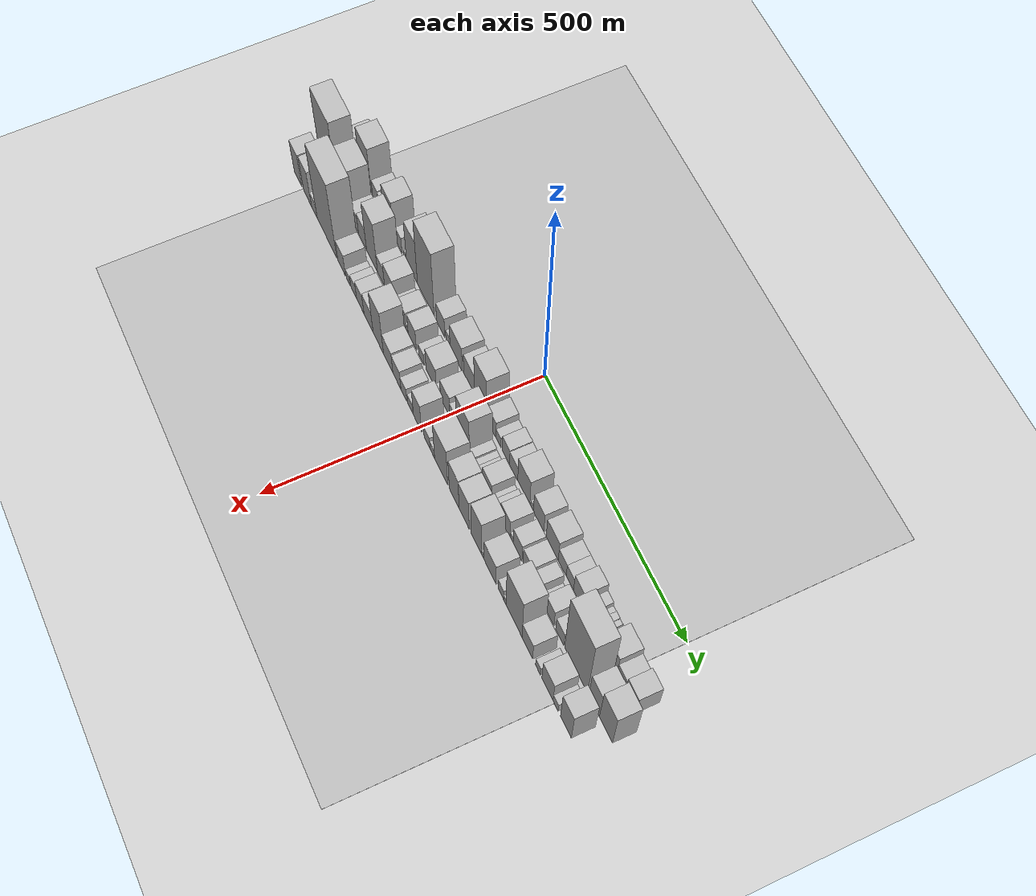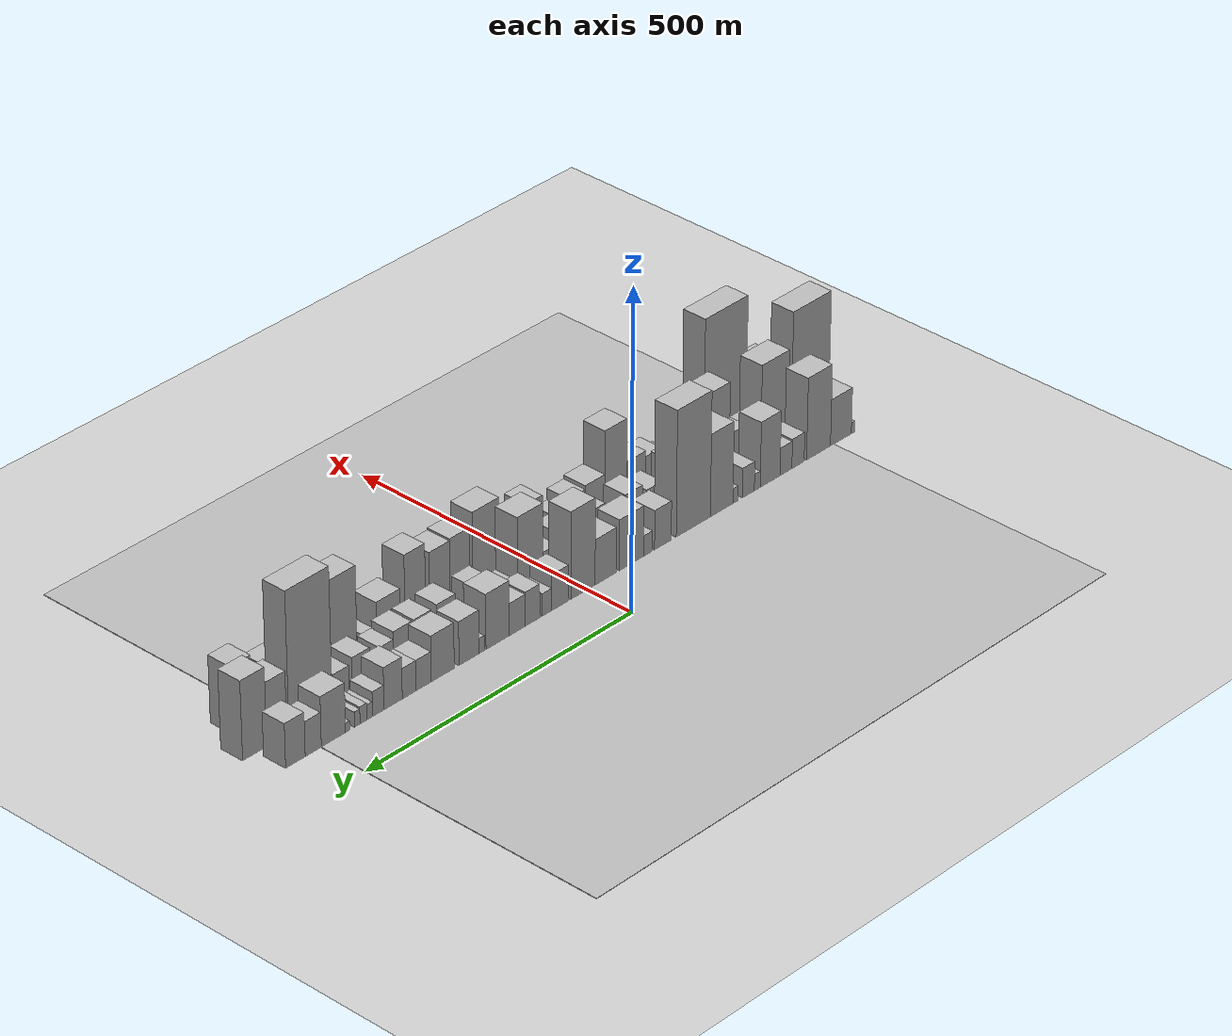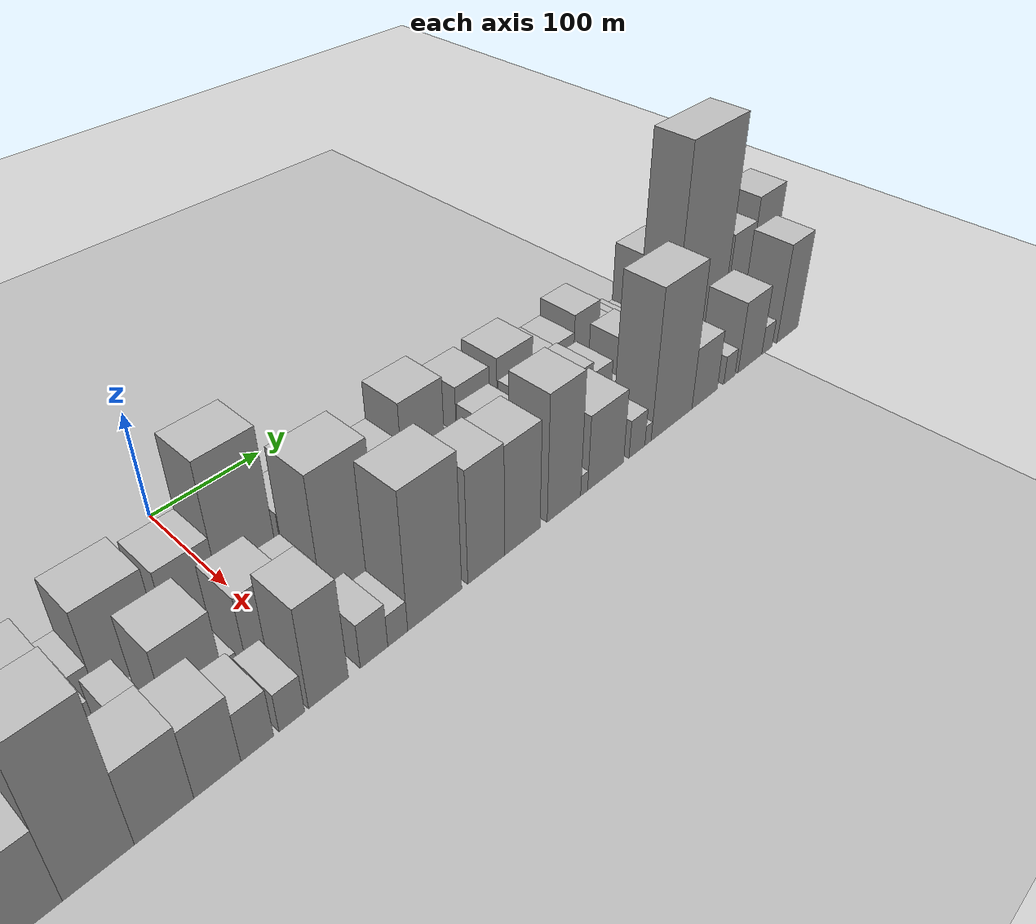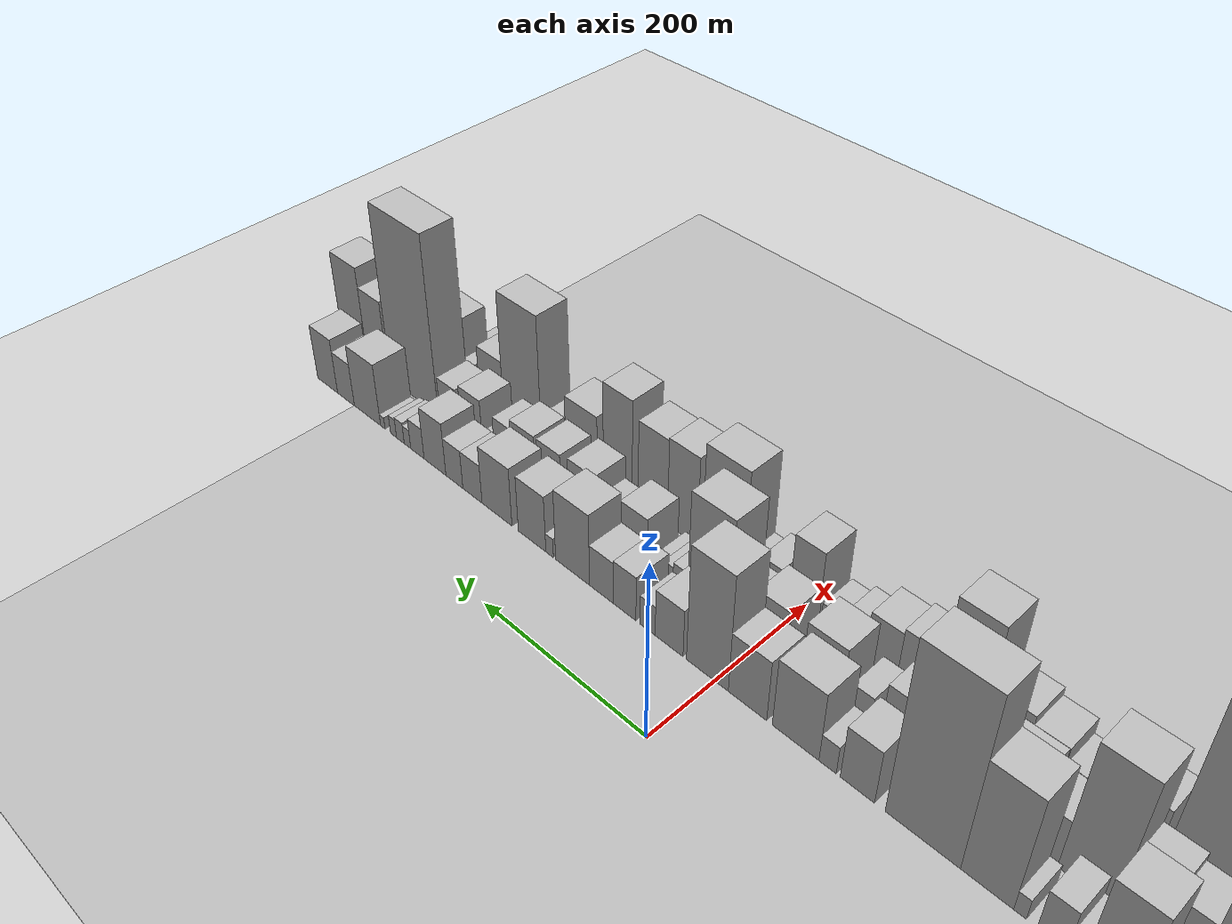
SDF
<?xml version="1.0" encoding="utf-8"?>

<sdf version="1.6">

   <world name="default">

      <gui fullscreen="0">

         <camera name="user_camera">

            <pose>-15 0 4.57585 0 0 0</pose>

            <view_controller>orbit</view_controller>

         </camera>

      </gui>

      <scene>

         <sky>

           <clouds>

             <speed>12</speed>

           </clouds>

         </sky>

         <ambient>0.4 0.4 0.4 1</ambient>

         <background>0.7 0.7 0.7 1</background>

         <shadows>1</shadows>

      </scene>

      <gravity>0 0 -9.8066</gravity>

      <magnetic_field>6e-06 2.3e-05 -4.2e-05</magnetic_field>

      <physics default="0" name="default_physics" type="ode">

         <ode>

            <solver>

               <type>quick</type>

               <iters>10</iters>

               <sor>1.0</sor>

               <use_dynamic_moi_rescaling>0</use_dynamic_moi_rescaling>

            </solver>

            <constraints>

               <cfm>0</cfm>

               <erp>0.2</erp>

               <contact_max_correcting_vel>100</contact_max_correcting_vel>

               <contact_surface_layer>0.001</contact_surface_layer>

            </constraints>

         </ode>

         <max_step_size>0.004</max_step_size>

         <real_time_factor>1</real_time_factor>

         <real_time_update_rate>250</real_time_update_rate>

      </physics>

      <light name="sun" type="directional">

         <cast_shadows>1</cast_shadows>

         <pose>0 0 10 0 0 0</pose>

         <diffuse>0.8 0.8 0.8 1</diffuse>

         <specular>0.2 0.2 0.2 1</specular>

         <attenuation>

            <range>1000</range>

            <constant>0.9</constant>

            <linear>0.01</linear>

            <quadratic>0.001</quadratic>

         </attenuation>

         <direction>-0.5 0.1 -0.9</direction>

      </light>

      <include>

         <name>ground_plane_1</name>

         <uri>model://HANNAS_ground_plane</uri>

         <pose>0 0 0  0 0 0</pose>

      </include>

      <include>

         <name>ground_plane_2</name>

         <uri>model://HANNAS_ground_plane</uri>

         <pose>100 0 0  0 0 0</pose>

      </include>

      <model name="building_1">

         <static>1</static>

         <pose frame="">100.0000 -540.2744 0 0.000000 0.000000 0.000000</pose>

         <link name="link">

            <pose frame="">0 0 9.00 0 0 0</pose>

            <collision name="collision">

               <geometry>

                  <box>

                     <size>40.0000 7.4513 18.0000</size>

                  </box>

               </geometry>

               <max_contacts>10</max_contacts>

               <surface>

                  <contact>

                     <ode/>

                  </contact>

                  <bounce/>

                  <friction>

                     <torsional>

                        <ode/>

                     </torsional>

                     <ode/>

                  </friction>

               </surface>

            </collision>

            <visual name="visual">

               <cast_shadows>0</cast_shadows>

               <geometry>

                  <box>

                     <size>40.0000 7.4513 18.0000</size>

                  </box>

               </geometry>

               <material>

                  <script>

                     <uri>model://HANNAS_wall/materials/scripts</uri>

                     <uri>model://HANNAS_wall/materials/textures</uri>

                     <name>vrc/HANNAS_wall</name>

                  </script>

               </material>

            </visual>

            <self_collide>0</self_collide>

            <enable_wind>0</enable_wind>

            <kinematic>0</kinematic>

         </link>

      </model>

      <model name="building_2">

         <static>1</static>

         <pose frame="">100.0000 -514.5848 0 0.000000 0.000000 0.000000</pose>

         <link name="link">

            <pose frame="">0 0 37.50 0 0 0</pose>

            <collision name="collision">

               <geometry>

                  <box>

                     <size>40.0000 43.9278 75.0000</size>

                  </box>

               </geometry>

               <max_contacts>10</max_contacts>

               <surface>

                  <contact>

                     <ode/>

                  </contact>

                  <bounce/>

                  <friction>

                     <torsional>

                        <ode/>

                     </torsional>

                     <ode/>

                  </friction>

               </surface>

            </collision>

            <visual name="visual">

               <cast_shadows>0</cast_shadows>

               <geometry>

                  <box>

                     <size>40.0000 43.9278 75.0000</size>

                  </box>

               </geometry>

               <material>

                  <script>

                     <uri>model://HANNAS_wall/materials/scripts</uri>

                     <uri>model://HANNAS_wall/materials/textures</uri>

                     <name>vrc/HANNAS_wall</name>

                  </script>

               </material>

            </visual>

            <self_collide>0</self_collide>

            <enable_wind>0</enable_wind>

            <kinematic>0</kinematic>

         </link>

      </model>

      <model name="building_3">

         <static>1</static>

         <pose frame="">100.0000 -467.5516 0 0.000000 0.000000 0.000000</pose>

         <link name="link">

            <pose frame="">0 0 66.00 0 0 0</pose>

            <collision name="collision">

               <geometry>

                  <box>

                     <size>40.0000 50.1385 132.0000</size>

                  </box>

               </geometry>

               <max_contacts>10</max_contacts>

               <surface>

                  <contact>

                     <ode/>

                  </contact>

                  <bounce/>

                  <friction>

                     <torsional>

                        <ode/>

                     </torsional>

                     <ode/>

                  </friction>

               </surface>

            </collision>

            <visual name="visual">

               <cast_shadows>0</cast_shadows>

               <geometry>

                  <box>

                     <size>40.0000 50.1385 132.0000</size>

                  </box>

               </geometry>

               <material>

                  <script>

                     <uri>model://HANNAS_wall/materials/scripts</uri>

                     <uri>model://HANNAS_wall/materials/textures</uri>

                     <name>vrc/HANNAS_wall</name>

                  </script>

               </material>

            </visual>

            <self_collide>0</self_collide>

            <enable_wind>0</enable_wind>

            <kinematic>0</kinematic>

         </link>

      </model>

      <model name="building_4">

         <static>1</static>

         <pose frame="">100.0000 -424.7385 0 0.000000 0.000000 0.000000</pose>

         <link name="link">

            <pose frame="">0 0 24.00 0 0 0</pose>

            <collision name="collision">

               <geometry>

                  <box>

                     <size>40.0000 25.4878 48.0000</size>

                  </box>

               </geometry>

               <max_contacts>10</max_contacts>

               <surface>

                  <contact>

                     <ode/>

                  </contact>

                  <bounce/>

                  <friction>

                     <torsional>

                        <ode/>

                     </torsional>

                     <ode/>

                  </friction>

               </surface>

            </collision>

            <visual name="visual">

               <cast_shadows>0</cast_shadows>

               <geometry>

                  <box>

                     <size>40.0000 25.4878 48.0000</size>

                  </box>

               </geometry>

               <material>

                  <script>

                     <uri>model://HANNAS_wall/materials/scripts</uri>

                     <uri>model://HANNAS_wall/materials/textures</uri>

                     <name>vrc/HANNAS_wall</name>

                  </script>

               </material>

            </visual>

            <self_collide>0</self_collide>

            <enable_wind>0</enable_wind>

            <kinematic>0</kinematic>

         </link>

      </model>

      <model name="building_5">

         <static>1</static>

         <pose frame="">100.0000 -399.7430 0 0.000000 0.000000 0.000000</pose>

         <link name="link">

            <pose frame="">0 0 22.50 0 0 0</pose>

            <collision name="collision">

               <geometry>

                  <box>

                     <size>40.0000 24.5031 45.0000</size>

                  </box>

               </geometry>

               <max_contacts>10</max_contacts>

               <surface>

                  <contact>

                     <ode/>

                  </contact>

                  <bounce/>

                  <friction>

                     <torsional>

                        <ode/>

                     </torsional>

                     <ode/>

                  </friction>

               </surface>

            </collision>

            <visual name="visual">

               <cast_shadows>0</cast_shadows>

               <geometry>

                  <box>

                     <size>40.0000 24.5031 45.0000</size>

                  </box>

               </geometry>

               <material>

                  <script>

                     <uri>model://HANNAS_wall/materials/scripts</uri>

                     <uri>model://HANNAS_wall/materials/textures</uri>

                     <name>vrc/HANNAS_wall</name>

                  </script>

               </material>

            </visual>

            <self_collide>0</self_collide>

            <enable_wind>0</enable_wind>

            <kinematic>0</kinematic>

         </link>

      </model>

      <model name="building_6">

         <static>1</static>

         <pose frame="">100.0000 -367.0211 0 0.000000 0.000000 0.000000</pose>

         <link name="link">

            <pose frame="">0 0 52.50 0 0 0</pose>

            <collision name="collision">

               <geometry>

                  <box>

                     <size>40.0000 40.9406 105.0000</size>

                  </box>

               </geometry>

               <max_contacts>10</max_contacts>

               <surface>

                  <contact>

                     <ode/>

                  </contact>

                  <bounce/>

                  <friction>

                     <torsional>

                        <ode/>

                     </torsional>

                     <ode/>

                  </friction>

               </surface>

            </collision>

            <visual name="visual">

               <cast_shadows>0</cast_shadows>

               <geometry>

                  <box>

                     <size>40.0000 40.9406 105.0000</size>

                  </box>

               </geometry>

               <material>

                  <script>

                     <uri>model://HANNAS_wall/materials/scripts</uri>

                     <uri>model://HANNAS_wall/materials/textures</uri>

                     <name>vrc/HANNAS_wall</name>

                  </script>

               </material>

            </visual>

            <self_collide>0</self_collide>

            <enable_wind>0</enable_wind>

            <kinematic>0</kinematic>

         </link>

      </model>

      <model name="building_7">

         <static>1</static>

         <pose frame="">100.0000 -340.4954 0 0.000000 0.000000 0.000000</pose>

         <link name="link">

            <pose frame="">0 0 13.50 0 0 0</pose>

            <collision name="collision">

               <geometry>

                  <box>

                     <size>40.0000 12.1108 27.0000</size>

                  </box>

               </geometry>

               <max_contacts>10</max_contacts>

               <surface>

                  <contact>

                     <ode/>

                  </contact>

                  <bounce/>

                  <friction>

                     <torsional>

                        <ode/>

                     </torsional>

                     <ode/>

                  </friction>

               </surface>

            </collision>

            <visual name="visual">

               <cast_shadows>0</cast_shadows>

               <geometry>

                  <box>

                     <size>40.0000 12.1108 27.0000</size>

                  </box>

               </geometry>

               <material>

                  <script>

                     <uri>model://HANNAS_wall/materials/scripts</uri>

                     <uri>model://HANNAS_wall/materials/textures</uri>

                     <name>vrc/HANNAS_wall</name>

                  </script>

               </material>

            </visual>

            <self_collide>0</self_collide>

            <enable_wind>0</enable_wind>

            <kinematic>0</kinematic>

         </link>

      </model>

      <model name="building_8">

         <static>1</static>

         <pose frame="">100.0000 -322.2776 0 0.000000 0.000000 0.000000</pose>

         <link name="link">

            <pose frame="">0 0 24.00 0 0 0</pose>

            <collision name="collision">

               <geometry>

                  <box>

                     <size>40.0000 24.3248 48.0000</size>

                  </box>

               </geometry>

               <max_contacts>10</max_contacts>

               <surface>

                  <contact>

                     <ode/>

                  </contact>

                  <bounce/>

                  <friction>

                     <torsional>

                        <ode/>

                     </torsional>

                     <ode/>

                  </friction>

               </surface>

            </collision>

            <visual name="visual">

               <cast_shadows>0</cast_shadows>

               <geometry>

                  <box>

                     <size>40.0000 24.3248 48.0000</size>

                  </box>

               </geometry>

               <material>

                  <script>

                     <uri>model://HANNAS_wall/materials/scripts</uri>

                     <uri>model://HANNAS_wall/materials/textures</uri>

                     <name>vrc/HANNAS_wall</name>

                  </script>

               </material>

            </visual>

            <self_collide>0</self_collide>

            <enable_wind>0</enable_wind>

            <kinematic>0</kinematic>

         </link>

      </model>

      <model name="building_9">

         <static>1</static>

         <pose frame="">100.0000 -295.8266 0 0.000000 0.000000 0.000000</pose>

         <link name="link">

            <pose frame="">0 0 12.00 0 0 0</pose>

            <collision name="collision">

               <geometry>

                  <box>

                     <size>40.0000 10.5772 24.0000</size>

                  </box>

               </geometry>

               <max_contacts>10</max_contacts>

               <surface>

                  <contact>

                     <ode/>

                  </contact>

                  <bounce/>

                  <friction>

                     <torsional>

                        <ode/>

                     </torsional>

                     <ode/>

                  </friction>

               </surface>

            </collision>

            <visual name="visual">

               <cast_shadows>0</cast_shadows>

               <geometry>

                  <box>

                     <size>40.0000 10.5772 24.0000</size>

                  </box>

               </geometry>

               <material>

                  <script>

                     <uri>model://HANNAS_wall/materials/scripts</uri>

                     <uri>model://HANNAS_wall/materials/textures</uri>

                     <name>vrc/HANNAS_wall</name>

                  </script>

               </material>

            </visual>

            <self_collide>0</self_collide>

            <enable_wind>0</enable_wind>

            <kinematic>0</kinematic>

         </link>

      </model>

      <model name="building_10">

         <static>1</static>

         <pose frame="">100.0000 -267.7011 0 0.000000 0.000000 0.000000</pose>

         <link name="link">

            <pose frame="">0 0 66.00 0 0 0</pose>

            <collision name="collision">

               <geometry>

                  <box>

                     <size>40.0000 45.6738 132.0000</size>

                  </box>

               </geometry>

               <max_contacts>10</max_contacts>

               <surface>

                  <contact>

                     <ode/>

                  </contact>

                  <bounce/>

                  <friction>

                     <torsional>

                        <ode/>

                     </torsional>

                     <ode/>

                  </friction>

               </surface>

            </collision>

            <visual name="visual">

               <cast_shadows>0</cast_shadows>

               <geometry>

                  <box>

                     <size>40.0000 45.6738 132.0000</size>

                  </box>

               </geometry>

               <material>

                  <script>

                     <uri>model://HANNAS_wall/materials/scripts</uri>

                     <uri>model://HANNAS_wall/materials/textures</uri>

                     <name>vrc/HANNAS_wall</name>

                  </script>

               </material>

            </visual>

            <self_collide>0</self_collide>

            <enable_wind>0</enable_wind>

            <kinematic>0</kinematic>

         </link>

      </model>

      <model name="building_11">

         <static>1</static>

         <pose frame="">100.0000 -210.4352 0 0.000000 0.000000 0.000000</pose>

         <link name="link">

            <pose frame="">0 0 100.50 0 0 0</pose>

            <collision name="collision">

               <geometry>

                  <box>

                     <size>40.0000 68.8580 201.0000</size>

                  </box>

               </geometry>

               <max_contacts>10</max_contacts>

               <surface>

                  <contact>

                     <ode/>

                  </contact>

                  <bounce/>

                  <friction>

                     <torsional>

                        <ode/>

                     </torsional>

                     <ode/>

                  </friction>

               </surface>

            </collision>

            <visual name="visual">

               <cast_shadows>0</cast_shadows>

               <geometry>

                  <box>

                     <size>40.0000 68.8580 201.0000</size>

                  </box>

               </geometry>

               <material>

                  <script>

                     <uri>model://HANNAS_wall/materials/scripts</uri>

                     <uri>model://HANNAS_wall/materials/textures</uri>

                     <name>vrc/HANNAS_wall</name>

                  </script>

               </material>

            </visual>

            <self_collide>0</self_collide>

            <enable_wind>0</enable_wind>

            <kinematic>0</kinematic>

         </link>

      </model>

      <model name="building_12">

         <static>1</static>

         <pose frame="">100.0000 -149.3027 0 0.000000 0.000000 0.000000</pose>

         <link name="link">

            <pose frame="">0 0 31.50 0 0 0</pose>

            <collision name="collision">

               <geometry>

                  <box>

                     <size>40.0000 33.4069 63.0000</size>

                  </box>

               </geometry>

               <max_contacts>10</max_contacts>

               <surface>

                  <contact>

                     <ode/>

                  </contact>

                  <bounce/>

                  <friction>

                     <torsional>

                        <ode/>

                     </torsional>

                     <ode/>

                  </friction>

               </surface>

            </collision>

            <visual name="visual">

               <cast_shadows>0</cast_shadows>

               <geometry>

                  <box>

                     <size>40.0000 33.4069 63.0000</size>

                  </box>

               </geometry>

               <material>

                  <script>

                     <uri>model://HANNAS_wall/materials/scripts</uri>

                     <uri>model://HANNAS_wall/materials/textures</uri>

                     <name>vrc/HANNAS_wall</name>

                  </script>

               </material>

            </visual>

            <self_collide>0</self_collide>

            <enable_wind>0</enable_wind>

            <kinematic>0</kinematic>

         </link>

      </model>

      <model name="building_13">

         <static>1</static>

         <pose frame="">100.0000 -119.9643 0 0.000000 0.000000 0.000000</pose>

         <link name="link">

            <pose frame="">0 0 16.50 0 0 0</pose>

            <collision name="collision">

               <geometry>

                  <box>

                     <size>40.0000 17.2699 33.0000</size>

                  </box>

               </geometry>

               <max_contacts>10</max_contacts>

               <surface>

                  <contact>

                     <ode/>

                  </contact>

                  <bounce/>

                  <friction>

                     <torsional>

                        <ode/>

                     </torsional>

                     <ode/>

                  </friction>

               </surface>

            </collision>

            <visual name="visual">

               <cast_shadows>0</cast_shadows>

               <geometry>

                  <box>

                     <size>40.0000 17.2699 33.0000</size>

                  </box>

               </geometry>

               <material>

                  <script>

                     <uri>model://HANNAS_wall/materials/scripts</uri>

                     <uri>model://HANNAS_wall/materials/textures</uri>

                     <name>vrc/HANNAS_wall</name>

                  </script>

               </material>

            </visual>

            <self_collide>0</self_collide>

            <enable_wind>0</enable_wind>

            <kinematic>0</kinematic>

         </link>

      </model>

      <model name="building_14">

         <static>1</static>

         <pose frame="">100.0000 -87.2110 0 0.000000 0.000000 0.000000</pose>

         <link name="link">

            <pose frame="">0 0 40.50 0 0 0</pose>

            <collision name="collision">

               <geometry>

                  <box>

                     <size>40.0000 48.2367 81.0000</size>

                  </box>

               </geometry>

               <max_contacts>10</max_contacts>

               <surface>

                  <contact>

                     <ode/>

                  </contact>

                  <bounce/>

                  <friction>

                     <torsional>

                        <ode/>

                     </torsional>

                     <ode/>

                  </friction>

               </surface>

            </collision>

            <visual name="visual">

               <cast_shadows>0</cast_shadows>

               <geometry>

                  <box>

                     <size>40.0000 48.2367 81.0000</size>

                  </box>

               </geometry>

               <material>

                  <script>

                     <uri>model://HANNAS_wall/materials/scripts</uri>

                     <uri>model://HANNAS_wall/materials/textures</uri>

                     <name>vrc/HANNAS_wall</name>

                  </script>

               </material>

            </visual>

            <self_collide>0</self_collide>

            <enable_wind>0</enable_wind>

            <kinematic>0</kinematic>

         </link>

      </model>

      <model name="building_15">

         <static>1</static>

         <pose frame="">100.0000 -36.2434 0 0.000000 0.000000 0.000000</pose>

         <link name="link">

            <pose frame="">0 0 36.00 0 0 0</pose>

            <collision name="collision">

               <geometry>

                  <box>

                     <size>40.0000 41.6985 72.0000</size>

                  </box>

               </geometry>

               <max_contacts>10</max_contacts>

               <surface>

                  <contact>

                     <ode/>

                  </contact>

                  <bounce/>

                  <friction>

                     <torsional>

                        <ode/>

                     </torsional>

                     <ode/>

                  </friction>

               </surface>

            </collision>

            <visual name="visual">

               <cast_shadows>0</cast_shadows>

               <geometry>

                  <box>

                     <size>40.0000 41.6985 72.0000</size>

                  </box>

               </geometry>

               <material>

                  <script>

                     <uri>model://HANNAS_wall/materials/scripts</uri>

                     <uri>model://HANNAS_wall/materials/textures</uri>

                     <name>vrc/HANNAS_wall</name>

                  </script>

               </material>

            </visual>

            <self_collide>0</self_collide>

            <enable_wind>0</enable_wind>

            <kinematic>0</kinematic>

         </link>

      </model>

      <model name="building_16">

         <static>1</static>

         <pose frame="">100.0000 8.3210 0 0.000000 0.000000 0.000000</pose>

         <link name="link">

            <pose frame="">0 0 69.00 0 0 0</pose>

            <collision name="collision">

               <geometry>

                  <box>

                     <size>40.0000 47.4301 138.0000</size>

                  </box>

               </geometry>

               <max_contacts>10</max_contacts>

               <surface>

                  <contact>

                     <ode/>

                  </contact>

                  <bounce/>

                  <friction>

                     <torsional>

                        <ode/>

                     </torsional>

                     <ode/>

                  </friction>

               </surface>

            </collision>

            <visual name="visual">

               <cast_shadows>0</cast_shadows>

               <geometry>

                  <box>

                     <size>40.0000 47.4301 138.0000</size>

                  </box>

               </geometry>

               <material>

                  <script>

                     <uri>model://HANNAS_wall/materials/scripts</uri>

                     <uri>model://HANNAS_wall/materials/textures</uri>

                     <name>vrc/HANNAS_wall</name>

                  </script>

               </material>

            </visual>

            <self_collide>0</self_collide>

            <enable_wind>0</enable_wind>

            <kinematic>0</kinematic>

         </link>

      </model>

      <model name="building_17">

         <static>1</static>

         <pose frame="">100.0000 52.4644 0 0.000000 0.000000 0.000000</pose>

         <link name="link">

            <pose frame="">0 0 28.50 0 0 0</pose>

            <collision name="collision">

               <geometry>

                  <box>

                     <size>40.0000 32.8567 57.0000</size>

                  </box>

               </geometry>

               <max_contacts>10</max_contacts>

               <surface>

                  <contact>

                     <ode/>

                  </contact>

                  <bounce/>

                  <friction>

                     <torsional>

                        <ode/>

                     </torsional>

                     <ode/>

                  </friction>

               </surface>

            </collision>

            <visual name="visual">

               <cast_shadows>0</cast_shadows>

               <geometry>

                  <box>

                     <size>40.0000 32.8567 57.0000</size>

                  </box>

               </geometry>

               <material>

                  <script>

                     <uri>model://HANNAS_wall/materials/scripts</uri>

                     <uri>model://HANNAS_wall/materials/textures</uri>

                     <name>vrc/HANNAS_wall</name>

                  </script>

               </material>

            </visual>

            <self_collide>0</self_collide>

            <enable_wind>0</enable_wind>

            <kinematic>0</kinematic>

         </link>

      </model>

      <model name="building_18">

         <static>1</static>

         <pose frame="">100.0000 78.0467 0 0.000000 0.000000 0.000000</pose>

         <link name="link">

            <pose frame="">0 0 18.00 0 0 0</pose>

            <collision name="collision">

               <geometry>

                  <box>

                     <size>40.0000 18.3079 36.0000</size>

                  </box>

               </geometry>

               <max_contacts>10</max_contacts>

               <surface>

                  <contact>

                     <ode/>

                  </contact>

                  <bounce/>

                  <friction>

                     <torsional>

                        <ode/>

                     </torsional>

                     <ode/>

                  </friction>

               </surface>

            </collision>

            <visual name="visual">

               <cast_shadows>0</cast_shadows>

               <geometry>

                  <box>

                     <size>40.0000 18.3079 36.0000</size>

                  </box>

               </geometry>

               <material>

                  <script>

                     <uri>model://HANNAS_wall/materials/scripts</uri>

                     <uri>model://HANNAS_wall/materials/textures</uri>

                     <name>vrc/HANNAS_wall</name>

                  </script>

               </material>

            </visual>

            <self_collide>0</self_collide>

            <enable_wind>0</enable_wind>

            <kinematic>0</kinematic>

         </link>

      </model>

      <model name="building_19">

         <static>1</static>

         <pose frame="">100.0000 106.0688 0 0.000000 0.000000 0.000000</pose>

         <link name="link">

            <pose frame="">0 0 27.00 0 0 0</pose>

            <collision name="collision">

               <geometry>

                  <box>

                     <size>40.0000 27.7362 54.0000</size>

                  </box>

               </geometry>

               <max_contacts>10</max_contacts>

               <surface>

                  <contact>

                     <ode/>

                  </contact>

                  <bounce/>

                  <friction>

                     <torsional>

                        <ode/>

                     </torsional>

                     <ode/>

                  </friction>

               </surface>

            </collision>

            <visual name="visual">

               <cast_shadows>0</cast_shadows>

               <geometry>

                  <box>

                     <size>40.0000 27.7362 54.0000</size>

                  </box>

               </geometry>

               <material>

                  <script>

                     <uri>model://HANNAS_wall/materials/scripts</uri>

                     <uri>model://HANNAS_wall/materials/textures</uri>

                     <name>vrc/HANNAS_wall</name>

                  </script>

               </material>

            </visual>

            <self_collide>0</self_collide>

            <enable_wind>0</enable_wind>

            <kinematic>0</kinematic>

         </link>

      </model>

      <model name="building_20">

         <static>1</static>

         <pose frame="">100.0000 135.0909 0 0.000000 0.000000 0.000000</pose>

         <link name="link">

            <pose frame="">0 0 25.50 0 0 0</pose>

            <collision name="collision">

               <geometry>

                  <box>

                     <size>40.0000 30.3081 51.0000</size>

                  </box>

               </geometry>

               <max_contacts>10</max_contacts>

               <surface>

                  <contact>

                     <ode/>

                  </contact>

                  <bounce/>

                  <friction>

                     <torsional>

                        <ode/>

                     </torsional>

                     <ode/>

                  </friction>

               </surface>

            </collision>

            <visual name="visual">

               <cast_shadows>0</cast_shadows>

               <geometry>

                  <box>

                     <size>40.0000 30.3081 51.0000</size>

                  </box>

               </geometry>

               <material>

                  <script>

                     <uri>model://HANNAS_wall/materials/scripts</uri>

                     <uri>model://HANNAS_wall/materials/textures</uri>

                     <name>vrc/HANNAS_wall</name>

                  </script>

               </material>

            </visual>

            <self_collide>0</self_collide>

            <enable_wind>0</enable_wind>

            <kinematic>0</kinematic>

         </link>

      </model>

      <model name="building_21">

         <static>1</static>

         <pose frame="">100.0000 172.5904 0 0.000000 0.000000 0.000000</pose>

         <link name="link">

            <pose frame="">0 0 43.50 0 0 0</pose>

            <collision name="collision">

               <geometry>

                  <box>

                     <size>40.0000 44.6907 87.0000</size>

                  </box>

               </geometry>

               <max_contacts>10</max_contacts>

               <surface>

                  <contact>

                     <ode/>

                  </contact>

                  <bounce/>

                  <friction>

                     <torsional>

                        <ode/>

                     </torsional>

                     <ode/>

                  </friction>

               </surface>

            </collision>

            <visual name="visual">

               <cast_shadows>0</cast_shadows>

               <geometry>

                  <box>

                     <size>40.0000 44.6907 87.0000</size>

                  </box>

               </geometry>

               <material>

                  <script>

                     <uri>model://HANNAS_wall/materials/scripts</uri>

                     <uri>model://HANNAS_wall/materials/textures</uri>

                     <name>vrc/HANNAS_wall</name>

                  </script>

               </material>

            </visual>

            <self_collide>0</self_collide>

            <enable_wind>0</enable_wind>

            <kinematic>0</kinematic>

         </link>

      </model>

      <model name="building_22">

         <static>1</static>

         <pose frame="">100.0000 203.0269 0 0.000000 0.000000 0.000000</pose>

         <link name="link">

            <pose frame="">0 0 12.00 0 0 0</pose>

            <collision name="collision">

               <geometry>

                  <box>

                     <size>40.0000 10.1823 24.0000</size>

                  </box>

               </geometry>

               <max_contacts>10</max_contacts>

               <surface>

                  <contact>

                     <ode/>

                  </contact>

                  <bounce/>

                  <friction>

                     <torsional>

                        <ode/>

                     </torsional>

                     <ode/>

                  </friction>

               </surface>

            </collision>

            <visual name="visual">

               <cast_shadows>0</cast_shadows>

               <geometry>

                  <box>

                     <size>40.0000 10.1823 24.0000</size>

                  </box>

               </geometry>

               <material>

                  <script>

                     <uri>model://HANNAS_wall/materials/scripts</uri>

                     <uri>model://HANNAS_wall/materials/textures</uri>

                     <name>vrc/HANNAS_wall</name>

                  </script>

               </material>

            </visual>

            <self_collide>0</self_collide>

            <enable_wind>0</enable_wind>

            <kinematic>0</kinematic>

         </link>

      </model>

      <model name="building_23">

         <static>1</static>

         <pose frame="">100.0000 227.0333 0 0.000000 0.000000 0.000000</pose>

         <link name="link">

            <pose frame="">0 0 34.50 0 0 0</pose>

            <collision name="collision">

               <geometry>

                  <box>

                     <size>40.0000 37.8305 69.0000</size>

                  </box>

               </geometry>

               <max_contacts>10</max_contacts>

               <surface>

                  <contact>

                     <ode/>

                  </contact>

                  <bounce/>

                  <friction>

                     <torsional>

                        <ode/>

                     </torsional>

                     <ode/>

                  </friction>

               </surface>

            </collision>

            <visual name="visual">

               <cast_shadows>0</cast_shadows>

               <geometry>

                  <box>

                     <size>40.0000 37.8305 69.0000</size>

                  </box>

               </geometry>

               <material>

                  <script>

                     <uri>model://HANNAS_wall/materials/scripts</uri>

                     <uri>model://HANNAS_wall/materials/textures</uri>

                     <name>vrc/HANNAS_wall</name>

                  </script>

               </material>

            </visual>

            <self_collide>0</self_collide>

            <enable_wind>0</enable_wind>

            <kinematic>0</kinematic>

         </link>

      </model>

      <model name="building_24">

         <static>1</static>

         <pose frame="">100.0000 276.3763 0 0.000000 0.000000 0.000000</pose>

         <link name="link">

            <pose frame="">0 0 36.00 0 0 0</pose>

            <collision name="collision">

               <geometry>

                  <box>

                     <size>40.0000 42.8556 72.0000</size>

                  </box>

               </geometry>

               <max_contacts>10</max_contacts>

               <surface>

                  <contact>

                     <ode/>

                  </contact>

                  <bounce/>

                  <friction>

                     <torsional>

                        <ode/>

                     </torsional>

                     <ode/>

                  </friction>

               </surface>

            </collision>

            <visual name="visual">

               <cast_shadows>0</cast_shadows>

               <geometry>

                  <box>

                     <size>40.0000 42.8556 72.0000</size>

                  </box>

               </geometry>

               <material>

                  <script>

                     <uri>model://HANNAS_wall/materials/scripts</uri>

                     <uri>model://HANNAS_wall/materials/textures</uri>

                     <name>vrc/HANNAS_wall</name>

                  </script>

               </material>

            </visual>

            <self_collide>0</self_collide>

            <enable_wind>0</enable_wind>

            <kinematic>0</kinematic>

         </link>

      </model>

      <model name="building_25">

         <static>1</static>

         <pose frame="">100.0000 311.9865 0 0.000000 0.000000 0.000000</pose>

         <link name="link">

            <pose frame="">0 0 24.00 0 0 0</pose>

            <collision name="collision">

               <geometry>

                  <box>

                     <size>40.0000 28.3647 48.0000</size>

                  </box>

               </geometry>

               <max_contacts>10</max_contacts>

               <surface>

                  <contact>

                     <ode/>

                  </contact>

                  <bounce/>

                  <friction>

                     <torsional>

                        <ode/>

                     </torsional>

                     <ode/>

                  </friction>

               </surface>

            </collision>

            <visual name="visual">

               <cast_shadows>0</cast_shadows>

               <geometry>

                  <box>

                     <size>40.0000 28.3647 48.0000</size>

                  </box>

               </geometry>

               <material>

                  <script>

                     <uri>model://HANNAS_wall/materials/scripts</uri>

                     <uri>model://HANNAS_wall/materials/textures</uri>

                     <name>vrc/HANNAS_wall</name>

                  </script>

               </material>

            </visual>

            <self_collide>0</self_collide>

            <enable_wind>0</enable_wind>

            <kinematic>0</kinematic>

         </link>

      </model>

      <model name="building_26">

         <static>1</static>

         <pose frame="">100.0000 338.9722 0 0.000000 0.000000 0.000000</pose>

         <link name="link">

            <pose frame="">0 0 24.00 0 0 0</pose>

            <collision name="collision">

               <geometry>

                  <box>

                     <size>40.0000 25.6068 48.0000</size>

                  </box>

               </geometry>

               <max_contacts>10</max_contacts>

               <surface>

                  <contact>

                     <ode/>

                  </contact>

                  <bounce/>

                  <friction>

                     <torsional>

                        <ode/>

                     </torsional>

                     <ode/>

                  </friction>

               </surface>

            </collision>

            <visual name="visual">

               <cast_shadows>0</cast_shadows>

               <geometry>

                  <box>

                     <size>40.0000 25.6068 48.0000</size>

                  </box>

               </geometry>

               <material>

                  <script>

                     <uri>model://HANNAS_wall/materials/scripts</uri>

                     <uri>model://HANNAS_wall/materials/textures</uri>

                     <name>vrc/HANNAS_wall</name>

                  </script>

               </material>

            </visual>

            <self_collide>0</self_collide>

            <enable_wind>0</enable_wind>

            <kinematic>0</kinematic>

         </link>

      </model>

      <model name="building_27">

         <static>1</static>

         <pose frame="">100.0000 368.6468 0 0.000000 0.000000 0.000000</pose>

         <link name="link">

            <pose frame="">0 0 33.00 0 0 0</pose>

            <collision name="collision">

               <geometry>

                  <box>

                     <size>40.0000 33.7423 66.0000</size>

                  </box>

               </geometry>

               <max_contacts>10</max_contacts>

               <surface>

                  <contact>

                     <ode/>

                  </contact>

                  <bounce/>

                  <friction>

                     <torsional>

                        <ode/>

                     </torsional>

                     <ode/>

                  </friction>

               </surface>

            </collision>

            <visual name="visual">

               <cast_shadows>0</cast_shadows>

               <geometry>

                  <box>

                     <size>40.0000 33.7423 66.0000</size>

                  </box>

               </geometry>

               <material>

                  <script>

                     <uri>model://HANNAS_wall/materials/scripts</uri>

                     <uri>model://HANNAS_wall/materials/textures</uri>

                     <name>vrc/HANNAS_wall</name>

                  </script>

               </material>

            </visual>

            <self_collide>0</self_collide>

            <enable_wind>0</enable_wind>

            <kinematic>0</kinematic>

         </link>

      </model>

      <model name="building_28">

         <static>1</static>

         <pose frame="">100.0000 396.0992 0 0.000000 0.000000 0.000000</pose>

         <link name="link">

            <pose frame="">0 0 19.50 0 0 0</pose>

            <collision name="collision">

               <geometry>

                  <box>

                     <size>40.0000 21.1626 39.0000</size>

                  </box>

               </geometry>

               <max_contacts>10</max_contacts>

               <surface>

                  <contact>

                     <ode/>

                  </contact>

                  <bounce/>

                  <friction>

                     <torsional>

                        <ode/>

                     </torsional>

                     <ode/>

                  </friction>

               </surface>

            </collision>

            <visual name="visual">

               <cast_shadows>0</cast_shadows>

               <geometry>

                  <box>

                     <size>40.0000 21.1626 39.0000</size>

                  </box>

               </geometry>

               <material>

                  <script>

                     <uri>model://HANNAS_wall/materials/scripts</uri>

                     <uri>model://HANNAS_wall/materials/textures</uri>

                     <name>vrc/HANNAS_wall</name>

                  </script>

               </material>

            </visual>

            <self_collide>0</self_collide>

            <enable_wind>0</enable_wind>

            <kinematic>0</kinematic>

         </link>

      </model>

      <model name="building_29">

         <static>1</static>

         <pose frame="">100.0000 411.8839 0 0.000000 0.000000 0.000000</pose>

         <link name="link">

            <pose frame="">0 0 12.00 0 0 0</pose>

            <collision name="collision">

               <geometry>

                  <box>

                     <size>40.0000 10.4068 24.0000</size>

                  </box>

               </geometry>

               <max_contacts>10</max_contacts>

               <surface>

                  <contact>

                     <ode/>

                  </contact>

                  <bounce/>

                  <friction>

                     <torsional>

                        <ode/>

                     </torsional>

                     <ode/>

                  </friction>

               </surface>

            </collision>

            <visual name="visual">

               <cast_shadows>0</cast_shadows>

               <geometry>

                  <box>

                     <size>40.0000 10.4068 24.0000</size>

                  </box>

               </geometry>

               <material>

                  <script>

                     <uri>model://HANNAS_wall/materials/scripts</uri>

                     <uri>model://HANNAS_wall/materials/textures</uri>

                     <name>vrc/HANNAS_wall</name>

                  </script>

               </material>

            </visual>

            <self_collide>0</self_collide>

            <enable_wind>0</enable_wind>

            <kinematic>0</kinematic>

         </link>

      </model>

      <model name="building_30">

         <static>1</static>

         <pose frame="">100.0000 423.3340 0 0.000000 0.000000 0.000000</pose>

         <link name="link">

            <pose frame="">0 0 13.50 0 0 0</pose>

            <collision name="collision">

               <geometry>

                  <box>

                     <size>40.0000 12.4933 27.0000</size>

                  </box>

               </geometry>

               <max_contacts>10</max_contacts>

               <surface>

                  <contact>

                     <ode/>

                  </contact>

                  <bounce/>

                  <friction>

                     <torsional>

                        <ode/>

                     </torsional>

                     <ode/>

                  </friction>

               </surface>

            </collision>

            <visual name="visual">

               <cast_shadows>0</cast_shadows>

               <geometry>

                  <box>

                     <size>40.0000 12.4933 27.0000</size>

                  </box>

               </geometry>

               <material>

                  <script>

                     <uri>model://HANNAS_wall/materials/scripts</uri>

                     <uri>model://HANNAS_wall/materials/textures</uri>

                     <name>vrc/HANNAS_wall</name>

                  </script>

               </material>

            </visual>

            <self_collide>0</self_collide>

            <enable_wind>0</enable_wind>

            <kinematic>0</kinematic>

         </link>

      </model>

      <model name="building_31">

         <static>1</static>

         <pose frame="">100.0000 434.4753 0 0.000000 0.000000 0.000000</pose>

         <link name="link">

            <pose frame="">0 0 12.00 0 0 0</pose>

            <collision name="collision">

               <geometry>

                  <box>

                     <size>40.0000 9.7893 24.0000</size>

                  </box>

               </geometry>

               <max_contacts>10</max_contacts>

               <surface>

                  <contact>

                     <ode/>

                  </contact>

                  <bounce/>

                  <friction>

                     <torsional>

                        <ode/>

                     </torsional>

                     <ode/>

                  </friction>

               </surface>

            </collision>

            <visual name="visual">

               <cast_shadows>0</cast_shadows>

               <geometry>

                  <box>

                     <size>40.0000 9.7893 24.0000</size>

                  </box>

               </geometry>

               <material>

                  <script>

                     <uri>model://HANNAS_wall/materials/scripts</uri>

                     <uri>model://HANNAS_wall/materials/textures</uri>

                     <name>vrc/HANNAS_wall</name>

                  </script>

               </material>

            </visual>

            <self_collide>0</self_collide>

            <enable_wind>0</enable_wind>

            <kinematic>0</kinematic>

         </link>

      </model>

      <model name="building_32">

         <static>1</static>

         <pose frame="">100.0000 452.1030 0 0.000000 0.000000 0.000000</pose>

         <link name="link">

            <pose frame="">0 0 7.50 0 0 0</pose>

            <collision name="collision">

               <geometry>

                  <box>

                     <size>40.0000 7.4662 15.0000</size>

                  </box>

               </geometry>

               <max_contacts>10</max_contacts>

               <surface>

                  <contact>

                     <ode/>

                  </contact>

                  <bounce/>

                  <friction>

                     <torsional>

                        <ode/>

                     </torsional>

                     <ode/>

                  </friction>

               </surface>

            </collision>

            <visual name="visual">

               <cast_shadows>0</cast_shadows>

               <geometry>

                  <box>

                     <size>40.0000 7.4662 15.0000</size>

                  </box>

               </geometry>

               <material>

                  <script>

                     <uri>model://HANNAS_wall/materials/scripts</uri>

                     <uri>model://HANNAS_wall/materials/textures</uri>

                     <name>vrc/HANNAS_wall</name>

                  </script>

               </material>

            </visual>

            <self_collide>0</self_collide>

            <enable_wind>0</enable_wind>

            <kinematic>0</kinematic>

         </link>

      </model>

      <model name="building_33">

         <static>1</static>

         <pose frame="">100.0000 477.8399 0 0.000000 0.000000 0.000000</pose>

         <link name="link">

            <pose frame="">0 0 39.00 0 0 0</pose>

            <collision name="collision">

               <geometry>

                  <box>

                     <size>40.0000 44.0075 78.0000</size>

                  </box>

               </geometry>

               <max_contacts>10</max_contacts>

               <surface>

                  <contact>

                     <ode/>

                  </contact>

                  <bounce/>

                  <friction>

                     <torsional>

                        <ode/>

                     </torsional>

                     <ode/>

                  </friction>

               </surface>

            </collision>

            <visual name="visual">

               <cast_shadows>0</cast_shadows>

               <geometry>

                  <box>

                     <size>40.0000 44.0075 78.0000</size>

                  </box>

               </geometry>

               <material>

                  <script>

                     <uri>model://HANNAS_wall/materials/scripts</uri>

                     <uri>model://HANNAS_wall/materials/textures</uri>

                     <name>vrc/HANNAS_wall</name>

                  </script>

               </material>

            </visual>

            <self_collide>0</self_collide>

            <enable_wind>0</enable_wind>

            <kinematic>0</kinematic>

         </link>

      </model>

      <model name="building_34">

         <static>1</static>

         <pose frame="">100.0000 514.4065 0 0.000000 0.000000 0.000000</pose>

         <link name="link">

            <pose frame="">0 0 27.00 0 0 0</pose>

            <collision name="collision">

               <geometry>

                  <box>

                     <size>40.0000 29.1258 54.0000</size>

                  </box>

               </geometry>

               <max_contacts>10</max_contacts>

               <surface>

                  <contact>

                     <ode/>

                  </contact>

                  <bounce/>

                  <friction>

                     <torsional>

                        <ode/>

                     </torsional>

                     <ode/>

                  </friction>

               </surface>

            </collision>

            <visual name="visual">

               <cast_shadows>0</cast_shadows>

               <geometry>

                  <box>

                     <size>40.0000 29.1258 54.0000</size>

                  </box>

               </geometry>

               <material>

                  <script>

                     <uri>model://HANNAS_wall/materials/scripts</uri>

                     <uri>model://HANNAS_wall/materials/textures</uri>

                     <name>vrc/HANNAS_wall</name>

                  </script>

               </material>

            </visual>

            <self_collide>0</self_collide>

            <enable_wind>0</enable_wind>

            <kinematic>0</kinematic>

         </link>

      </model>

      <model name="building_35">

         <static>1</static>

         <pose frame="">100.0000 546.5808 0 0.000000 0.000000 0.000000</pose>

         <link name="link">

            <pose frame="">0 0 34.50 0 0 0</pose>

            <collision name="collision">

               <geometry>

                  <box>

                     <size>40.0000 35.2226 69.0000</size>

                  </box>

               </geometry>

               <max_contacts>10</max_contacts>

               <surface>

                  <contact>

                     <ode/>

                  </contact>

                  <bounce/>

                  <friction>

                     <torsional>

                        <ode/>

                     </torsional>

                     <ode/>

                  </friction>

               </surface>

            </collision>

            <visual name="visual">

               <cast_shadows>0</cast_shadows>

               <geometry>

                  <box>

                     <size>40.0000 35.2226 69.0000</size>

                  </box>

               </geometry>

               <material>

                  <script>

                     <uri>model://HANNAS_wall/materials/scripts</uri>

                     <uri>model://HANNAS_wall/materials/textures</uri>

                     <name>vrc/HANNAS_wall</name>

                  </script>

               </material>

            </visual>

            <self_collide>0</self_collide>

            <enable_wind>0</enable_wind>

            <kinematic>0</kinematic>

         </link>

      </model>

      <model name="building_36">

         <static>1</static>

         <pose frame="">152.0000 -508.6156 0 0.000000 0.000000 0.000000</pose>

         <link name="link">

            <pose frame="">0 0 102.00 0 0 0</pose>

            <collision name="collision">

               <geometry>

                  <box>

                     <size>40.0000 78.7689 204.0000</size>

                  </box>

               </geometry>

               <max_contacts>10</max_contacts>

               <surface>

                  <contact>

                     <ode/>

                  </contact>

                  <bounce/>

                  <friction>

                     <torsional>

                        <ode/>

                     </torsional>

                     <ode/>

                  </friction>

               </surface>

            </collision>

            <visual name="visual">

               <cast_shadows>0</cast_shadows>

               <geometry>

                  <box>

                     <size>40.0000 78.7689 204.0000</size>

                  </box>

               </geometry>

               <material>

                  <script>

                     <uri>model://HANNAS_wall/materials/scripts</uri>

                     <uri>model://HANNAS_wall/materials/textures</uri>

                     <name>vrc/HANNAS_wall</name>

                  </script>

               </material>

            </visual>

            <self_collide>0</self_collide>

            <enable_wind>0</enable_wind>

            <kinematic>0</kinematic>

         </link>

      </model>

      <model name="building_37">

         <static>1</static>

         <pose frame="">152.0000 -434.7023 0 0.000000 0.000000 0.000000</pose>

         <link name="link">

            <pose frame="">0 0 73.50 0 0 0</pose>

            <collision name="collision">

               <geometry>

                  <box>

                     <size>40.0000 57.0577 147.0000</size>

                  </box>

               </geometry>

               <max_contacts>10</max_contacts>

               <surface>

                  <contact>

                     <ode/>

                  </contact>

                  <bounce/>

                  <friction>

                     <torsional>

                        <ode/>

                     </torsional>

                     <ode/>

                  </friction>

               </surface>

            </collision>

            <visual name="visual">

               <cast_shadows>0</cast_shadows>

               <geometry>

                  <box>

                     <size>40.0000 57.0577 147.0000</size>

                  </box>

               </geometry>

               <material>

                  <script>

                     <uri>model://HANNAS_wall/materials/scripts</uri>

                     <uri>model://HANNAS_wall/materials/textures</uri>

                     <name>vrc/HANNAS_wall</name>

                  </script>

               </material>

            </visual>

            <self_collide>0</self_collide>

            <enable_wind>0</enable_wind>

            <kinematic>0</kinematic>

         </link>

      </model>

      <model name="building_38">

         <static>1</static>

         <pose frame="">152.0000 -390.9776 0 0.000000 0.000000 0.000000</pose>

         <link name="link">

            <pose frame="">0 0 28.50 0 0 0</pose>

            <collision name="collision">

               <geometry>

                  <box>

                     <size>40.0000 30.3916 57.0000</size>

                  </box>

               </geometry>

               <max_contacts>10</max_contacts>

               <surface>

                  <contact>

                     <ode/>

                  </contact>

                  <bounce/>

                  <friction>

                     <torsional>

                        <ode/>

                     </torsional>

                     <ode/>

                  </friction>

               </surface>

            </collision>

            <visual name="visual">

               <cast_shadows>0</cast_shadows>

               <geometry>

                  <box>

                     <size>40.0000 30.3916 57.0000</size>

                  </box>

               </geometry>

               <material>

                  <script>

                     <uri>model://HANNAS_wall/materials/scripts</uri>

                     <uri>model://HANNAS_wall/materials/textures</uri>

                     <name>vrc/HANNAS_wall</name>

                  </script>

               </material>

            </visual>

            <self_collide>0</self_collide>

            <enable_wind>0</enable_wind>

            <kinematic>0</kinematic>

         </link>

      </model>

      <model name="building_39">

         <static>1</static>

         <pose frame="">152.0000 -358.3233 0 0.000000 0.000000 0.000000</pose>

         <link name="link">

            <pose frame="">0 0 33.00 0 0 0</pose>

            <collision name="collision">

               <geometry>

                  <box>

                     <size>40.0000 34.9169 66.0000</size>

                  </box>

               </geometry>

               <max_contacts>10</max_contacts>

               <surface>

                  <contact>

                     <ode/>

                  </contact>

                  <bounce/>

                  <friction>

                     <torsional>

                        <ode/>

                     </torsional>

                     <ode/>

                  </friction>

               </surface>

            </collision>

            <visual name="visual">

               <cast_shadows>0</cast_shadows>

               <geometry>

                  <box>

                     <size>40.0000 34.9169 66.0000</size>

                  </box>

               </geometry>

               <material>

                  <script>

                     <uri>model://HANNAS_wall/materials/scripts</uri>

                     <uri>model://HANNAS_wall/materials/textures</uri>

                     <name>vrc/HANNAS_wall</name>

                  </script>

               </material>

            </visual>

            <self_collide>0</self_collide>

            <enable_wind>0</enable_wind>

            <kinematic>0</kinematic>

         </link>

      </model>

      <model name="building_40">

         <static>1</static>

         <pose frame="">152.0000 -317.4290 0 0.000000 0.000000 0.000000</pose>

         <link name="link">

            <pose frame="">0 0 75.00 0 0 0</pose>

            <collision name="collision">

               <geometry>

                  <box>

                     <size>40.0000 46.8718 150.0000</size>

                  </box>

               </geometry>

               <max_contacts>10</max_contacts>

               <surface>

                  <contact>

                     <ode/>

                  </contact>

                  <bounce/>

                  <friction>

                     <torsional>

                        <ode/>

                     </torsional>

                     <ode/>

                  </friction>

               </surface>

            </collision>

            <visual name="visual">

               <cast_shadows>0</cast_shadows>

               <geometry>

                  <box>

                     <size>40.0000 46.8718 150.0000</size>

                  </box>

               </geometry>

               <material>

                  <script>

                     <uri>model://HANNAS_wall/materials/scripts</uri>

                     <uri>model://HANNAS_wall/materials/textures</uri>

                     <name>vrc/HANNAS_wall</name>

                  </script>

               </material>

            </visual>

            <self_collide>0</self_collide>

            <enable_wind>0</enable_wind>

            <kinematic>0</kinematic>

         </link>

      </model>

      <model name="building_41">

         <static>1</static>

         <pose frame="">152.0000 -278.8720 0 0.000000 0.000000 0.000000</pose>

         <link name="link">

            <pose frame="">0 0 28.50 0 0 0</pose>

            <collision name="collision">

               <geometry>

                  <box>

                     <size>40.0000 30.2423 57.0000</size>

                  </box>

               </geometry>

               <max_contacts>10</max_contacts>

               <surface>

                  <contact>

                     <ode/>

                  </contact>

                  <bounce/>

                  <friction>

                     <torsional>

                        <ode/>

                     </torsional>

                     <ode/>

                  </friction>

               </surface>

            </collision>

            <visual name="visual">

               <cast_shadows>0</cast_shadows>

               <geometry>

                  <box>

                     <size>40.0000 30.2423 57.0000</size>

                  </box>

               </geometry>

               <material>

                  <script>

                     <uri>model://HANNAS_wall/materials/scripts</uri>

                     <uri>model://HANNAS_wall/materials/textures</uri>

                     <name>vrc/HANNAS_wall</name>

                  </script>

               </material>

            </visual>

            <self_collide>0</self_collide>

            <enable_wind>0</enable_wind>

            <kinematic>0</kinematic>

         </link>

      </model>

      <model name="building_42">

         <static>1</static>

         <pose frame="">152.0000 -244.8094 0 0.000000 0.000000 0.000000</pose>

         <link name="link">

            <pose frame="">0 0 37.50 0 0 0</pose>

            <collision name="collision">

               <geometry>

                  <box>

                     <size>40.0000 37.8830 75.0000</size>

                  </box>

               </geometry>

               <max_contacts>10</max_contacts>

               <surface>

                  <contact>

                     <ode/>

                  </contact>

                  <bounce/>

                  <friction>

                     <torsional>

                        <ode/>

                     </torsional>

                     <ode/>

                  </friction>

               </surface>

            </collision>

            <visual name="visual">

               <cast_shadows>0</cast_shadows>

               <geometry>

                  <box>

                     <size>40.0000 37.8830 75.0000</size>

                  </box>

               </geometry>

               <material>

                  <script>

                     <uri>model://HANNAS_wall/materials/scripts</uri>

                     <uri>model://HANNAS_wall/materials/textures</uri>

                     <name>vrc/HANNAS_wall</name>

                  </script>

               </material>

            </visual>

            <self_collide>0</self_collide>

            <enable_wind>0</enable_wind>

            <kinematic>0</kinematic>

         </link>

      </model>

      <model name="building_43">

         <static>1</static>

         <pose frame="">152.0000 -220.2934 0 0.000000 0.000000 0.000000</pose>

         <link name="link">

            <pose frame="">0 0 13.50 0 0 0</pose>

            <collision name="collision">

               <geometry>

                  <box>

                     <size>40.0000 11.1489 27.0000</size>

                  </box>

               </geometry>

               <max_contacts>10</max_contacts>

               <surface>

                  <contact>

                     <ode/>

                  </contact>

                  <bounce/>

                  <friction>

                     <torsional>

                        <ode/>

                     </torsional>

                     <ode/>

                  </friction>

               </surface>

            </collision>

            <visual name="visual">

               <cast_shadows>0</cast_shadows>

               <geometry>

                  <box>

                     <size>40.0000 11.1489 27.0000</size>

                  </box>

               </geometry>

               <material>

                  <script>

                     <uri>model://HANNAS_wall/materials/scripts</uri>

                     <uri>model://HANNAS_wall/materials/textures</uri>

                     <name>vrc/HANNAS_wall</name>

                  </script>

               </material>

            </visual>

            <self_collide>0</self_collide>

            <enable_wind>0</enable_wind>

            <kinematic>0</kinematic>

         </link>

      </model>

      <model name="building_44">

         <static>1</static>

         <pose frame="">152.0000 -189.7533 0 0.000000 0.000000 0.000000</pose>

         <link name="link">

            <pose frame="">0 0 27.00 0 0 0</pose>

            <collision name="collision">

               <geometry>

                  <box>

                     <size>40.0000 31.9314 54.0000</size>

                  </box>

               </geometry>

               <max_contacts>10</max_contacts>

               <surface>

                  <contact>

                     <ode/>

                  </contact>

                  <bounce/>

                  <friction>

                     <torsional>

                        <ode/>

                     </torsional>

                     <ode/>

                  </friction>

               </surface>

            </collision>

            <visual name="visual">

               <cast_shadows>0</cast_shadows>

               <geometry>

                  <box>

                     <size>40.0000 31.9314 54.0000</size>

                  </box>

               </geometry>

               <material>

                  <script>

                     <uri>model://HANNAS_wall/materials/scripts</uri>

                     <uri>model://HANNAS_wall/materials/textures</uri>

                     <name>vrc/HANNAS_wall</name>

                  </script>

               </material>

            </visual>

            <self_collide>0</self_collide>

            <enable_wind>0</enable_wind>

            <kinematic>0</kinematic>

         </link>

      </model>

      <model name="building_45">

         <static>1</static>

         <pose frame="">152.0000 -169.3819 0 0.000000 0.000000 0.000000</pose>

         <link name="link">

            <pose frame="">0 0 10.50 0 0 0</pose>

            <collision name="collision">

               <geometry>

                  <box>

                     <size>40.0000 8.8114 21.0000</size>

                  </box>

               </geometry>

               <max_contacts>10</max_contacts>

               <surface>

                  <contact>

                     <ode/>

                  </contact>

                  <bounce/>

                  <friction>

                     <torsional>

                        <ode/>

                     </torsional>

                     <ode/>

                  </friction>

               </surface>

            </collision>

            <visual name="visual">

               <cast_shadows>0</cast_shadows>

               <geometry>

                  <box>

                     <size>40.0000 8.8114 21.0000</size>

                  </box>

               </geometry>

               <material>

                  <script>

                     <uri>model://HANNAS_wall/materials/scripts</uri>

                     <uri>model://HANNAS_wall/materials/textures</uri>

                     <name>vrc/HANNAS_wall</name>

                  </script>

               </material>

            </visual>

            <self_collide>0</self_collide>

            <enable_wind>0</enable_wind>

            <kinematic>0</kinematic>

         </link>

      </model>

      <model name="building_46">

         <static>1</static>

         <pose frame="">152.0000 -148.0550 0 0.000000 0.000000 0.000000</pose>

         <link name="link">

            <pose frame="">0 0 33.00 0 0 0</pose>

            <collision name="collision">

               <geometry>

                  <box>

                     <size>40.0000 33.8424 66.0000</size>

                  </box>

               </geometry>

               <max_contacts>10</max_contacts>

               <surface>

                  <contact>

                     <ode/>

                  </contact>

                  <bounce/>

                  <friction>

                     <torsional>

                        <ode/>

                     </torsional>

                     <ode/>

                  </friction>

               </surface>

            </collision>

            <visual name="visual">

               <cast_shadows>0</cast_shadows>

               <geometry>

                  <box>

                     <size>40.0000 33.8424 66.0000</size>

                  </box>

               </geometry>

               <material>

                  <script>

                     <uri>model://HANNAS_wall/materials/scripts</uri>

                     <uri>model://HANNAS_wall/materials/textures</uri>

                     <name>vrc/HANNAS_wall</name>

                  </script>

               </material>

            </visual>

            <self_collide>0</self_collide>

            <enable_wind>0</enable_wind>

            <kinematic>0</kinematic>

         </link>

      </model>

      <model name="building_47">

         <static>1</static>

         <pose frame="">152.0000 -110.4191 0 0.000000 0.000000 0.000000</pose>

         <link name="link">

            <pose frame="">0 0 19.50 0 0 0</pose>

            <collision name="collision">

               <geometry>

                  <box>

                     <size>40.0000 21.4294 39.0000</size>

                  </box>

               </geometry>

               <max_contacts>10</max_contacts>

               <surface>

                  <contact>

                     <ode/>

                  </contact>

                  <bounce/>

                  <friction>

                     <torsional>

                        <ode/>

                     </torsional>

                     <ode/>

                  </friction>

               </surface>

            </collision>

            <visual name="visual">

               <cast_shadows>0</cast_shadows>

               <geometry>

                  <box>

                     <size>40.0000 21.4294 39.0000</size>

                  </box>

               </geometry>

               <material>

                  <script>

                     <uri>model://HANNAS_wall/materials/scripts</uri>

                     <uri>model://HANNAS_wall/materials/textures</uri>

                     <name>vrc/HANNAS_wall</name>

                  </script>

               </material>

            </visual>

            <self_collide>0</self_collide>

            <enable_wind>0</enable_wind>

            <kinematic>0</kinematic>

         </link>

      </model>

      <model name="building_48">

         <static>1</static>

         <pose frame="">152.0000 -70.9050 0 0.000000 0.000000 0.000000</pose>

         <link name="link">

            <pose frame="">0 0 36.00 0 0 0</pose>

            <collision name="collision">

               <geometry>

                  <box>

                     <size>40.0000 41.5988 72.0000</size>

                  </box>

               </geometry>

               <max_contacts>10</max_contacts>

               <surface>

                  <contact>

                     <ode/>

                  </contact>

                  <bounce/>

                  <friction>

                     <torsional>

                        <ode/>

                     </torsional>

                     <ode/>

                  </friction>

               </surface>

            </collision>

            <visual name="visual">

               <cast_shadows>0</cast_shadows>

               <geometry>

                  <box>

                     <size>40.0000 41.5988 72.0000</size>

                  </box>

               </geometry>

               <material>

                  <script>

                     <uri>model://HANNAS_wall/materials/scripts</uri>

                     <uri>model://HANNAS_wall/materials/textures</uri>

                     <name>vrc/HANNAS_wall</name>

                  </script>

               </material>

            </visual>

            <self_collide>0</self_collide>

            <enable_wind>0</enable_wind>

            <kinematic>0</kinematic>

         </link>

      </model>

      <model name="building_49">

         <static>1</static>

         <pose frame="">152.0000 -44.6371 0 0.000000 0.000000 0.000000</pose>

         <link name="link">

            <pose frame="">0 0 12.00 0 0 0</pose>

            <collision name="collision">

               <geometry>

                  <box>

                     <size>40.0000 10.9370 24.0000</size>

                  </box>

               </geometry>

               <max_contacts>10</max_contacts>

               <surface>

                  <contact>

                     <ode/>

                  </contact>

                  <bounce/>

                  <friction>

                     <torsional>

                        <ode/>

                     </torsional>

                     <ode/>

                  </friction>

               </surface>

            </collision>

            <visual name="visual">

               <cast_shadows>0</cast_shadows>

               <geometry>

                  <box>

                     <size>40.0000 10.9370 24.0000</size>

                  </box>

               </geometry>

               <material>

                  <script>

                     <uri>model://HANNAS_wall/materials/scripts</uri>

                     <uri>model://HANNAS_wall/materials/textures</uri>

                     <name>vrc/HANNAS_wall</name>

                  </script>

               </material>

            </visual>

            <self_collide>0</self_collide>

            <enable_wind>0</enable_wind>

            <kinematic>0</kinematic>

         </link>

      </model>

      <model name="building_50">

         <static>1</static>

         <pose frame="">152.0000 -14.9263 0 0.000000 0.000000 0.000000</pose>

         <link name="link">

            <pose frame="">0 0 34.50 0 0 0</pose>

            <collision name="collision">

               <geometry>

                  <box>

                     <size>40.0000 36.4846 69.0000</size>

                  </box>

               </geometry>

               <max_contacts>10</max_contacts>

               <surface>

                  <contact>

                     <ode/>

                  </contact>

                  <bounce/>

                  <friction>

                     <torsional>

                        <ode/>

                     </torsional>

                     <ode/>

                  </friction>

               </surface>

            </collision>

            <visual name="visual">

               <cast_shadows>0</cast_shadows>

               <geometry>

                  <box>

                     <size>40.0000 36.4846 69.0000</size>

                  </box>

               </geometry>

               <material>

                  <script>

                     <uri>model://HANNAS_wall/materials/scripts</uri>

                     <uri>model://HANNAS_wall/materials/textures</uri>

                     <name>vrc/HANNAS_wall</name>

                  </script>

               </material>

            </visual>

            <self_collide>0</self_collide>

            <enable_wind>0</enable_wind>

            <kinematic>0</kinematic>

         </link>

      </model>

      <model name="building_51">

         <static>1</static>

         <pose frame="">152.0000 16.5949 0 0.000000 0.000000 0.000000</pose>

         <link name="link">

            <pose frame="">0 0 25.50 0 0 0</pose>

            <collision name="collision">

               <geometry>

                  <box>

                     <size>40.0000 26.5579 51.0000</size>

                  </box>

               </geometry>

               <max_contacts>10</max_contacts>

               <surface>

                  <contact>

                     <ode/>

                  </contact>

                  <bounce/>

                  <friction>

                     <torsional>

                        <ode/>

                     </torsional>

                     <ode/>

                  </friction>

               </surface>

            </collision>

            <visual name="visual">

               <cast_shadows>0</cast_shadows>

               <geometry>

                  <box>

                     <size>40.0000 26.5579 51.0000</size>

                  </box>

               </geometry>

               <material>

                  <script>

                     <uri>model://HANNAS_wall/materials/scripts</uri>

                     <uri>model://HANNAS_wall/materials/textures</uri>

                     <name>vrc/HANNAS_wall</name>

                  </script>

               </material>

            </visual>

            <self_collide>0</self_collide>

            <enable_wind>0</enable_wind>

            <kinematic>0</kinematic>

         </link>

      </model>

      <model name="building_52">

         <static>1</static>

         <pose frame="">152.0000 54.8650 0 0.000000 0.000000 0.000000</pose>

         <link name="link">

            <pose frame="">0 0 64.50 0 0 0</pose>

            <collision name="collision">

               <geometry>

                  <box>

                     <size>40.0000 49.9821 129.0000</size>

                  </box>

               </geometry>

               <max_contacts>10</max_contacts>

               <surface>

                  <contact>

                     <ode/>

                  </contact>

                  <bounce/>

                  <friction>

                     <torsional>

                        <ode/>

                     </torsional>

                     <ode/>

                  </friction>

               </surface>

            </collision>

            <visual name="visual">

               <cast_shadows>0</cast_shadows>

               <geometry>

                  <box>

                     <size>40.0000 49.9821 129.0000</size>

                  </box>

               </geometry>

               <material>

                  <script>

                     <uri>model://HANNAS_wall/materials/scripts</uri>

                     <uri>model://HANNAS_wall/materials/textures</uri>

                     <name>vrc/HANNAS_wall</name>

                  </script>

               </material>

            </visual>

            <self_collide>0</self_collide>

            <enable_wind>0</enable_wind>

            <kinematic>0</kinematic>

         </link>

      </model>

      <model name="building_53">

         <static>1</static>

         <pose frame="">152.0000 88.7823 0 0.000000 0.000000 0.000000</pose>

         <link name="link">

            <pose frame="">0 0 15.00 0 0 0</pose>

            <collision name="collision">

               <geometry>

                  <box>

                     <size>40.0000 17.8526 30.0000</size>

                  </box>

               </geometry>

               <max_contacts>10</max_contacts>

               <surface>

                  <contact>

                     <ode/>

                  </contact>

                  <bounce/>

                  <friction>

                     <torsional>

                        <ode/>

                     </torsional>

                     <ode/>

                  </friction>

               </surface>

            </collision>

            <visual name="visual">

               <cast_shadows>0</cast_shadows>

               <geometry>

                  <box>

                     <size>40.0000 17.8526 30.0000</size>

                  </box>

               </geometry>

               <material>

                  <script>

                     <uri>model://HANNAS_wall/materials/scripts</uri>

                     <uri>model://HANNAS_wall/materials/textures</uri>

                     <name>vrc/HANNAS_wall</name>

                  </script>

               </material>

            </visual>

            <self_collide>0</self_collide>

            <enable_wind>0</enable_wind>

            <kinematic>0</kinematic>

         </link>

      </model>

      <model name="building_54">

         <static>1</static>

         <pose frame="">152.0000 103.6320 0 0.000000 0.000000 0.000000</pose>

         <link name="link">

            <pose frame="">0 0 12.00 0 0 0</pose>

            <collision name="collision">

               <geometry>

                  <box>

                     <size>40.0000 11.8467 24.0000</size>

                  </box>

               </geometry>

               <max_contacts>10</max_contacts>

               <surface>

                  <contact>

                     <ode/>

                  </contact>

                  <bounce/>

                  <friction>

                     <torsional>

                        <ode/>

                     </torsional>

                     <ode/>

                  </friction>

               </surface>

            </collision>

            <visual name="visual">

               <cast_shadows>0</cast_shadows>

               <geometry>

                  <box>

                     <size>40.0000 11.8467 24.0000</size>

                  </box>

               </geometry>

               <material>

                  <script>

                     <uri>model://HANNAS_wall/materials/scripts</uri>

                     <uri>model://HANNAS_wall/materials/textures</uri>

                     <name>vrc/HANNAS_wall</name>

                  </script>

               </material>

            </visual>

            <self_collide>0</self_collide>

            <enable_wind>0</enable_wind>

            <kinematic>0</kinematic>

         </link>

      </model>

      <model name="building_55">

         <static>1</static>

         <pose frame="">152.0000 115.1448 0 0.000000 0.000000 0.000000</pose>

         <link name="link">

            <pose frame="">0 0 12.00 0 0 0</pose>

            <collision name="collision">

               <geometry>

                  <box>

                     <size>40.0000 11.1787 24.0000</size>

                  </box>

               </geometry>

               <max_contacts>10</max_contacts>

               <surface>

                  <contact>

                     <ode/>

                  </contact>

                  <bounce/>

                  <friction>

                     <torsional>

                        <ode/>

                     </torsional>

                     <ode/>

                  </friction>

               </surface>

            </collision>

            <visual name="visual">

               <cast_shadows>0</cast_shadows>

               <geometry>

                  <box>

                     <size>40.0000 11.1787 24.0000</size>

                  </box>

               </geometry>

               <material>

                  <script>

                     <uri>model://HANNAS_wall/materials/scripts</uri>

                     <uri>model://HANNAS_wall/materials/textures</uri>

                     <name>vrc/HANNAS_wall</name>

                  </script>

               </material>

            </visual>

            <self_collide>0</self_collide>

            <enable_wind>0</enable_wind>

            <kinematic>0</kinematic>

         </link>

      </model>

      <model name="building_56">

         <static>1</static>

         <pose frame="">152.0000 147.0022 0 0.000000 0.000000 0.000000</pose>

         <link name="link">

            <pose frame="">0 0 30.00 0 0 0</pose>

            <collision name="collision">

               <geometry>

                  <box>

                     <size>40.0000 34.5362 60.0000</size>

                  </box>

               </geometry>

               <max_contacts>10</max_contacts>

               <surface>

                  <contact>

                     <ode/>

                  </contact>

                  <bounce/>

                  <friction>

                     <torsional>

                        <ode/>

                     </torsional>

                     <ode/>

                  </friction>

               </surface>

            </collision>

            <visual name="visual">

               <cast_shadows>0</cast_shadows>

               <geometry>

                  <box>

                     <size>40.0000 34.5362 60.0000</size>

                  </box>

               </geometry>

               <material>

                  <script>

                     <uri>model://HANNAS_wall/materials/scripts</uri>

                     <uri>model://HANNAS_wall/materials/textures</uri>

                     <name>vrc/HANNAS_wall</name>

                  </script>

               </material>

            </visual>

            <self_collide>0</self_collide>

            <enable_wind>0</enable_wind>

            <kinematic>0</kinematic>

         </link>

      </model>

      <model name="building_57">

         <static>1</static>

         <pose frame="">152.0000 170.9954 0 0.000000 0.000000 0.000000</pose>

         <link name="link">

            <pose frame="">0 0 13.50 0 0 0</pose>

            <collision name="collision">

               <geometry>

                  <box>

                     <size>40.0000 13.4503 27.0000</size>

                  </box>

               </geometry>

               <max_contacts>10</max_contacts>

               <surface>

                  <contact>

                     <ode/>

                  </contact>

                  <bounce/>

                  <friction>

                     <torsional>

                        <ode/>

                     </torsional>

                     <ode/>

                  </friction>

               </surface>

            </collision>

            <visual name="visual">

               <cast_shadows>0</cast_shadows>

               <geometry>

                  <box>

                     <size>40.0000 13.4503 27.0000</size>

                  </box>

               </geometry>

               <material>

                  <script>

                     <uri>model://HANNAS_wall/materials/scripts</uri>

                     <uri>model://HANNAS_wall/materials/textures</uri>

                     <name>vrc/HANNAS_wall</name>

                  </script>

               </material>

            </visual>

            <self_collide>0</self_collide>

            <enable_wind>0</enable_wind>

            <kinematic>0</kinematic>

         </link>

      </model>

      <model name="building_58">

         <static>1</static>

         <pose frame="">152.0000 187.7708 0 0.000000 0.000000 0.000000</pose>

         <link name="link">

            <pose frame="">0 0 19.50 0 0 0</pose>

            <collision name="collision">

               <geometry>

                  <box>

                     <size>40.0000 20.1006 39.0000</size>

                  </box>

               </geometry>

               <max_contacts>10</max_contacts>

               <surface>

                  <contact>

                     <ode/>

                  </contact>

                  <bounce/>

                  <friction>

                     <torsional>

                        <ode/>

                     </torsional>

                     <ode/>

                  </friction>

               </surface>

            </collision>

            <visual name="visual">

               <cast_shadows>0</cast_shadows>

               <geometry>

                  <box>

                     <size>40.0000 20.1006 39.0000</size>

                  </box>

               </geometry>

               <material>

                  <script>

                     <uri>model://HANNAS_wall/materials/scripts</uri>

                     <uri>model://HANNAS_wall/materials/textures</uri>

                     <name>vrc/HANNAS_wall</name>

                  </script>

               </material>

            </visual>

            <self_collide>0</self_collide>

            <enable_wind>0</enable_wind>

            <kinematic>0</kinematic>

         </link>

      </model>

      <model name="building_59">

         <static>1</static>

         <pose frame="">152.0000 215.5120 0 0.000000 0.000000 0.000000</pose>

         <link name="link">

            <pose frame="">0 0 33.00 0 0 0</pose>

            <collision name="collision">

               <geometry>

                  <box>

                     <size>40.0000 35.3817 66.0000</size>

                  </box>

               </geometry>

               <max_contacts>10</max_contacts>

               <surface>

                  <contact>

                     <ode/>

                  </contact>

                  <bounce/>

                  <friction>

                     <torsional>

                        <ode/>

                     </torsional>

                     <ode/>

                  </friction>

               </surface>

            </collision>

            <visual name="visual">

               <cast_shadows>0</cast_shadows>

               <geometry>

                  <box>

                     <size>40.0000 35.3817 66.0000</size>

                  </box>

               </geometry>

               <material>

                  <script>

                     <uri>model://HANNAS_wall/materials/scripts</uri>

                     <uri>model://HANNAS_wall/materials/textures</uri>

                     <name>vrc/HANNAS_wall</name>

                  </script>

               </material>

            </visual>

            <self_collide>0</self_collide>

            <enable_wind>0</enable_wind>

            <kinematic>0</kinematic>

         </link>

      </model>

      <model name="building_60">

         <static>1</static>

         <pose frame="">152.0000 238.4505 0 0.000000 0.000000 0.000000</pose>

         <link name="link">

            <pose frame="">0 0 12.00 0 0 0</pose>

            <collision name="collision">

               <geometry>

                  <box>

                     <size>40.0000 10.4954 24.0000</size>

                  </box>

               </geometry>

               <max_contacts>10</max_contacts>

               <surface>

                  <contact>

                     <ode/>

                  </contact>

                  <bounce/>

                  <friction>

                     <torsional>

                        <ode/>

                     </torsional>

                     <ode/>

                  </friction>

               </surface>

            </collision>

            <visual name="visual">

               <cast_shadows>0</cast_shadows>

               <geometry>

                  <box>

                     <size>40.0000 10.4954 24.0000</size>

                  </box>

               </geometry>

               <material>

                  <script>

                     <uri>model://HANNAS_wall/materials/scripts</uri>

                     <uri>model://HANNAS_wall/materials/textures</uri>

                     <name>vrc/HANNAS_wall</name>

                  </script>

               </material>

            </visual>

            <self_collide>0</self_collide>

            <enable_wind>0</enable_wind>

            <kinematic>0</kinematic>

         </link>

      </model>

      <model name="building_61">

         <static>1</static>

         <pose frame="">152.0000 259.8015 0 0.000000 0.000000 0.000000</pose>

         <link name="link">

            <pose frame="">0 0 31.50 0 0 0</pose>

            <collision name="collision">

               <geometry>

                  <box>

                     <size>40.0000 32.2067 63.0000</size>

                  </box>

               </geometry>

               <max_contacts>10</max_contacts>

               <surface>

                  <contact>

                     <ode/>

                  </contact>

                  <bounce/>

                  <friction>

                     <torsional>

                        <ode/>

                     </torsional>

                     <ode/>

                  </friction>

               </surface>

            </collision>

            <visual name="visual">

               <cast_shadows>0</cast_shadows>

               <geometry>

                  <box>

                     <size>40.0000 32.2067 63.0000</size>

                  </box>

               </geometry>

               <material>

                  <script>

                     <uri>model://HANNAS_wall/materials/scripts</uri>

                     <uri>model://HANNAS_wall/materials/textures</uri>

                     <name>vrc/HANNAS_wall</name>

                  </script>

               </material>

            </visual>

            <self_collide>0</self_collide>

            <enable_wind>0</enable_wind>

            <kinematic>0</kinematic>

         </link>

      </model>

      <model name="building_62">

         <static>1</static>

         <pose frame="">152.0000 297.1086 0 0.000000 0.000000 0.000000</pose>

         <link name="link">

            <pose frame="">0 0 31.50 0 0 0</pose>

            <collision name="collision">

               <geometry>

                  <box>

                     <size>40.0000 34.4074 63.0000</size>

                  </box>

               </geometry>

               <max_contacts>10</max_contacts>

               <surface>

                  <contact>

                     <ode/>

                  </contact>

                  <bounce/>

                  <friction>

                     <torsional>

                        <ode/>

                     </torsional>

                     <ode/>

                  </friction>

               </surface>

            </collision>

            <visual name="visual">

               <cast_shadows>0</cast_shadows>

               <geometry>

                  <box>

                     <size>40.0000 34.4074 63.0000</size>

                  </box>

               </geometry>

               <material>

                  <script>

                     <uri>model://HANNAS_wall/materials/scripts</uri>

                     <uri>model://HANNAS_wall/materials/textures</uri>

                     <name>vrc/HANNAS_wall</name>

                  </script>

               </material>

            </visual>

            <self_collide>0</self_collide>

            <enable_wind>0</enable_wind>

            <kinematic>0</kinematic>

         </link>

      </model>

      <model name="building_63">

         <static>1</static>

         <pose frame="">152.0000 327.1191 0 0.000000 0.000000 0.000000</pose>

         <link name="link">

            <pose frame="">0 0 25.50 0 0 0</pose>

            <collision name="collision">

               <geometry>

                  <box>

                     <size>40.0000 25.6136 51.0000</size>

                  </box>

               </geometry>

               <max_contacts>10</max_contacts>

               <surface>

                  <contact>

                     <ode/>

                  </contact>

                  <bounce/>

                  <friction>

                     <torsional>

                        <ode/>

                     </torsional>

                     <ode/>

                  </friction>

               </surface>

            </collision>

            <visual name="visual">

               <cast_shadows>0</cast_shadows>

               <geometry>

                  <box>

                     <size>40.0000 25.6136 51.0000</size>

                  </box>

               </geometry>

               <material>

                  <script>

                     <uri>model://HANNAS_wall/materials/scripts</uri>

                     <uri>model://HANNAS_wall/materials/textures</uri>

                     <name>vrc/HANNAS_wall</name>

                  </script>

               </material>

            </visual>

            <self_collide>0</self_collide>

            <enable_wind>0</enable_wind>

            <kinematic>0</kinematic>

         </link>

      </model>

      <model name="building_64">

         <static>1</static>

         <pose frame="">152.0000 344.4212 0 0.000000 0.000000 0.000000</pose>

         <link name="link">

            <pose frame="">0 0 9.00 0 0 0</pose>

            <collision name="collision">

               <geometry>

                  <box>

                     <size>40.0000 8.9906 18.0000</size>

                  </box>

               </geometry>

               <max_contacts>10</max_contacts>

               <surface>

                  <contact>

                     <ode/>

                  </contact>

                  <bounce/>

                  <friction>

                     <torsional>

                        <ode/>

                     </torsional>

                     <ode/>

                  </friction>

               </surface>

            </collision>

            <visual name="visual">

               <cast_shadows>0</cast_shadows>

               <geometry>

                  <box>

                     <size>40.0000 8.9906 18.0000</size>

                  </box>

               </geometry>

               <material>

                  <script>

                     <uri>model://HANNAS_wall/materials/scripts</uri>

                     <uri>model://HANNAS_wall/materials/textures</uri>

                     <name>vrc/HANNAS_wall</name>

                  </script>

               </material>

            </visual>

            <self_collide>0</self_collide>

            <enable_wind>0</enable_wind>

            <kinematic>0</kinematic>

         </link>

      </model>

      <model name="building_65">

         <static>1</static>

         <pose frame="">152.0000 353.5203 0 0.000000 0.000000 0.000000</pose>

         <link name="link">

            <pose frame="">0 0 10.50 0 0 0</pose>

            <collision name="collision">

               <geometry>

                  <box>

                     <size>40.0000 9.2078 21.0000</size>

                  </box>

               </geometry>

               <max_contacts>10</max_contacts>

               <surface>

                  <contact>

                     <ode/>

                  </contact>

                  <bounce/>

                  <friction>

                     <torsional>

                        <ode/>

                     </torsional>

                     <ode/>

                  </friction>

               </surface>

            </collision>

            <visual name="visual">

               <cast_shadows>0</cast_shadows>

               <geometry>

                  <box>

                     <size>40.0000 9.2078 21.0000</size>

                  </box>

               </geometry>

               <material>

                  <script>

                     <uri>model://HANNAS_wall/materials/scripts</uri>

                     <uri>model://HANNAS_wall/materials/textures</uri>

                     <name>vrc/HANNAS_wall</name>

                  </script>

               </material>

            </visual>

            <self_collide>0</self_collide>

            <enable_wind>0</enable_wind>

            <kinematic>0</kinematic>

         </link>

      </model>

      <model name="building_66">

         <static>1</static>

         <pose frame="">152.0000 374.3418 0 0.000000 0.000000 0.000000</pose>

         <link name="link">

            <pose frame="">0 0 30.00 0 0 0</pose>

            <collision name="collision">

               <geometry>

                  <box>

                     <size>40.0000 32.4352 60.0000</size>

                  </box>

               </geometry>

               <max_contacts>10</max_contacts>

               <surface>

                  <contact>

                     <ode/>

                  </contact>

                  <bounce/>

                  <friction>

                     <torsional>

                        <ode/>

                     </torsional>

                     <ode/>

                  </friction>

               </surface>

            </collision>

            <visual name="visual">

               <cast_shadows>0</cast_shadows>

               <geometry>

                  <box>

                     <size>40.0000 32.4352 60.0000</size>

                  </box>

               </geometry>

               <material>

                  <script>

                     <uri>model://HANNAS_wall/materials/scripts</uri>

                     <uri>model://HANNAS_wall/materials/textures</uri>

                     <name>vrc/HANNAS_wall</name>

                  </script>

               </material>

            </visual>

            <self_collide>0</self_collide>

            <enable_wind>0</enable_wind>

            <kinematic>0</kinematic>

         </link>

      </model>

      <model name="building_67">

         <static>1</static>

         <pose frame="">152.0000 410.7092 0 0.000000 0.000000 0.000000</pose>

         <link name="link">

            <pose frame="">0 0 25.50 0 0 0</pose>

            <collision name="collision">

               <geometry>

                  <box>

                     <size>40.0000 28.2995 51.0000</size>

                  </box>

               </geometry>

               <max_contacts>10</max_contacts>

               <surface>

                  <contact>

                     <ode/>

                  </contact>

                  <bounce/>

                  <friction>

                     <torsional>

                        <ode/>

                     </torsional>

                     <ode/>

                  </friction>

               </surface>

            </collision>

            <visual name="visual">

               <cast_shadows>0</cast_shadows>

               <geometry>

                  <box>

                     <size>40.0000 28.2995 51.0000</size>

                  </box>

               </geometry>

               <material>

                  <script>

                     <uri>model://HANNAS_wall/materials/scripts</uri>

                     <uri>model://HANNAS_wall/materials/textures</uri>

                     <name>vrc/HANNAS_wall</name>

                  </script>

               </material>

            </visual>

            <self_collide>0</self_collide>

            <enable_wind>0</enable_wind>

            <kinematic>0</kinematic>

         </link>

      </model>

      <model name="building_68">

         <static>1</static>

         <pose frame="">152.0000 467.1438 0 0.000000 0.000000 0.000000</pose>

         <link name="link">

            <pose frame="">0 0 109.50 0 0 0</pose>

            <collision name="collision">

               <geometry>

                  <box>

                     <size>40.0000 78.5698 219.0000</size>

                  </box>

               </geometry>

               <max_contacts>10</max_contacts>

               <surface>

                  <contact>

                     <ode/>

                  </contact>

                  <bounce/>

                  <friction>

                     <torsional>

                        <ode/>

                     </torsional>

                     <ode/>

                  </friction>

               </surface>

            </collision>

            <visual name="visual">

               <cast_shadows>0</cast_shadows>

               <geometry>

                  <box>

                     <size>40.0000 78.5698 219.0000</size>

                  </box>

               </geometry>

               <material>

                  <script>

                     <uri>model://HANNAS_wall/materials/scripts</uri>

                     <uri>model://HANNAS_wall/materials/textures</uri>

                     <name>vrc/HANNAS_wall</name>

                  </script>

               </material>

            </visual>

            <self_collide>0</self_collide>

            <enable_wind>0</enable_wind>

            <kinematic>0</kinematic>

         </link>

      </model>

      <model name="building_69">

         <static>1</static>

         <pose frame="">152.0000 528.4487 0 0.000000 0.000000 0.000000</pose>

         <link name="link">

            <pose frame="">0 0 49.50 0 0 0</pose>

            <collision name="collision">

               <geometry>

                  <box>

                     <size>40.0000 36.0399 99.0000</size>

                  </box>

               </geometry>

               <max_contacts>10</max_contacts>

               <surface>

                  <contact>

                     <ode/>

                  </contact>

                  <bounce/>

                  <friction>

                     <torsional>

                        <ode/>

                     </torsional>

                     <ode/>

                  </friction>

               </surface>

            </collision>

            <visual name="visual">

               <cast_shadows>0</cast_shadows>

               <geometry>

                  <box>

                     <size>40.0000 36.0399 99.0000</size>

                  </box>

               </geometry>

               <material>

                  <script>

                     <uri>model://HANNAS_wall/materials/scripts</uri>

                     <uri>model://HANNAS_wall/materials/textures</uri>

                     <name>vrc/HANNAS_wall</name>

                  </script>

               </material>

            </visual>

            <self_collide>0</self_collide>

            <enable_wind>0</enable_wind>

            <kinematic>0</kinematic>

         </link>

      </model>

      <model name="building_70">

         <static>1</static>

         <pose frame="">152.0000 568.1302 0 0.000000 0.000000 0.000000</pose>

         <link name="link">

            <pose frame="">0 0 61.50 0 0 0</pose>

            <collision name="collision">

               <geometry>

                  <box>

                     <size>40.0000 43.3233 123.0000</size>

                  </box>

               </geometry>

               <max_contacts>10</max_contacts>

               <surface>

                  <contact>

                     <ode/>

                  </contact>

                  <bounce/>

                  <friction>

                     <torsional>

                        <ode/>

                     </torsional>

                     <ode/>

                  </friction>

               </surface>

            </collision>

            <visual name="visual">

               <cast_shadows>0</cast_shadows>

               <geometry>

                  <box>

                     <size>40.0000 43.3233 123.0000</size>

                  </box>

               </geometry>

               <material>

                  <script>

                     <uri>model://HANNAS_wall/materials/scripts</uri>

                     <uri>model://HANNAS_wall/materials/textures</uri>

                     <name>vrc/HANNAS_wall</name>

                  </script>

               </material>

            </visual>

            <self_collide>0</self_collide>

            <enable_wind>0</enable_wind>

            <kinematic>0</kinematic>

         </link>

      </model>

      <model name="building_71">

         <static>1</static>

         <pose frame="">204.0000 -521.5749 0 0.000000 0.000000 0.000000</pose>

         <link name="link">

            <pose frame="">0 0 48.00 0 0 0</pose>

            <collision name="collision">

               <geometry>

                  <box>

                     <size>40.0000 34.8501 96.0000</size>

                  </box>

               </geometry>

               <max_contacts>10</max_contacts>

               <surface>

                  <contact>

                     <ode/>

                  </contact>

                  <bounce/>

                  <friction>

                     <torsional>

                        <ode/>

                     </torsional>

                     <ode/>

                  </friction>

               </surface>

            </collision>

            <visual name="visual">

               <cast_shadows>0</cast_shadows>

               <geometry>

                  <box>

                     <size>40.0000 34.8501 96.0000</size>

                  </box>

               </geometry>

               <material>

                  <script>

                     <uri>model://HANNAS_wall/materials/scripts</uri>

                     <uri>model://HANNAS_wall/materials/textures</uri>

                     <name>vrc/HANNAS_wall</name>

                  </script>

               </material>

            </visual>

            <self_collide>0</self_collide>

            <enable_wind>0</enable_wind>

            <kinematic>0</kinematic>

         </link>

      </model>

      <model name="building_72">

         <static>1</static>

         <pose frame="">204.0000 -478.0240 0 0.000000 0.000000 0.000000</pose>

         <link name="link">

            <pose frame="">0 0 52.50 0 0 0</pose>

            <collision name="collision">

               <geometry>

                  <box>

                     <size>40.0000 36.2518 105.0000</size>

                  </box>

               </geometry>

               <max_contacts>10</max_contacts>

               <surface>

                  <contact>

                     <ode/>

                  </contact>

                  <bounce/>

                  <friction>

                     <torsional>

                        <ode/>

                     </torsional>

                     <ode/>

                  </friction>

               </surface>

            </collision>

            <visual name="visual">

               <cast_shadows>0</cast_shadows>

               <geometry>

                  <box>

                     <size>40.0000 36.2518 105.0000</size>

                  </box>

               </geometry>

               <material>

                  <script>

                     <uri>model://HANNAS_wall/materials/scripts</uri>

                     <uri>model://HANNAS_wall/materials/textures</uri>

                     <name>vrc/HANNAS_wall</name>

                  </script>

               </material>

            </visual>

            <self_collide>0</self_collide>

            <enable_wind>0</enable_wind>

            <kinematic>0</kinematic>

         </link>

      </model>

      <model name="building_73">

         <static>1</static>

         <pose frame="">204.0000 -447.0243 0 0.000000 0.000000 0.000000</pose>

         <link name="link">

            <pose frame="">0 0 22.50 0 0 0</pose>

            <collision name="collision">

               <geometry>

                  <box>

                     <size>40.0000 25.7476 45.0000</size>

                  </box>

               </geometry>

               <max_contacts>10</max_contacts>

               <surface>

                  <contact>

                     <ode/>

                  </contact>

                  <bounce/>

                  <friction>

                     <torsional>

                        <ode/>

                     </torsional>

                     <ode/>

                  </friction>

               </surface>

            </collision>

            <visual name="visual">

               <cast_shadows>0</cast_shadows>

               <geometry>

                  <box>

                     <size>40.0000 25.7476 45.0000</size>

                  </box>

               </geometry>

               <material>

                  <script>

                     <uri>model://HANNAS_wall/materials/scripts</uri>

                     <uri>model://HANNAS_wall/materials/textures</uri>

                     <name>vrc/HANNAS_wall</name>

                  </script>

               </material>

            </visual>

            <self_collide>0</self_collide>

            <enable_wind>0</enable_wind>

            <kinematic>0</kinematic>

         </link>

      </model>

      <model name="building_74">

         <static>1</static>

         <pose frame="">204.0000 -390.6399 0 0.000000 0.000000 0.000000</pose>

         <link name="link">

            <pose frame="">0 0 112.50 0 0 0</pose>

            <collision name="collision">

               <geometry>

                  <box>

                     <size>40.0000 87.0211 225.0000</size>

                  </box>

               </geometry>

               <max_contacts>10</max_contacts>

               <surface>

                  <contact>

                     <ode/>

                  </contact>

                  <bounce/>

                  <friction>

                     <torsional>

                        <ode/>

                     </torsional>

                     <ode/>

                  </friction>

               </surface>

            </collision>

            <visual name="visual">

               <cast_shadows>0</cast_shadows>

               <geometry>

                  <box>

                     <size>40.0000 87.0211 225.0000</size>

                  </box>

               </geometry>

               <material>

                  <script>

                     <uri>model://HANNAS_wall/materials/scripts</uri>

                     <uri>model://HANNAS_wall/materials/textures</uri>

                     <name>vrc/HANNAS_wall</name>

                  </script>

               </material>

            </visual>

            <self_collide>0</self_collide>

            <enable_wind>0</enable_wind>

            <kinematic>0</kinematic>

         </link>

      </model>

      <model name="building_75">

         <static>1</static>

         <pose frame="">204.0000 -325.4194 0 0.000000 0.000000 0.000000</pose>

         <link name="link">

            <pose frame="">0 0 33.00 0 0 0</pose>

            <collision name="collision">

               <geometry>

                  <box>

                     <size>40.0000 33.4198 66.0000</size>

                  </box>

               </geometry>

               <max_contacts>10</max_contacts>

               <surface>

                  <contact>

                     <ode/>

                  </contact>

                  <bounce/>

                  <friction>

                     <torsional>

                        <ode/>

                     </torsional>

                     <ode/>

                  </friction>

               </surface>

            </collision>

            <visual name="visual">

               <cast_shadows>0</cast_shadows>

               <geometry>

                  <box>

                     <size>40.0000 33.4198 66.0000</size>

                  </box>

               </geometry>

               <material>

                  <script>

                     <uri>model://HANNAS_wall/materials/scripts</uri>

                     <uri>model://HANNAS_wall/materials/textures</uri>

                     <name>vrc/HANNAS_wall</name>

                  </script>

               </material>

            </visual>

            <self_collide>0</self_collide>

            <enable_wind>0</enable_wind>

            <kinematic>0</kinematic>

         </link>

      </model>

      <model name="building_76">

         <static>1</static>

         <pose frame="">204.0000 -296.8877 0 0.000000 0.000000 0.000000</pose>

         <link name="link">

            <pose frame="">0 0 15.00 0 0 0</pose>

            <collision name="collision">

               <geometry>

                  <box>

                     <size>40.0000 15.6437 30.0000</size>

                  </box>

               </geometry>

               <max_contacts>10</max_contacts>

               <surface>

                  <contact>

                     <ode/>

                  </contact>

                  <bounce/>

                  <friction>

                     <torsional>

                        <ode/>

                     </torsional>

                     <ode/>

                  </friction>

               </surface>

            </collision>

            <visual name="visual">

               <cast_shadows>0</cast_shadows>

               <geometry>

                  <box>

                     <size>40.0000 15.6437 30.0000</size>

                  </box>

               </geometry>

               <material>

                  <script>

                     <uri>model://HANNAS_wall/materials/scripts</uri>

                     <uri>model://HANNAS_wall/materials/textures</uri>

                     <name>vrc/HANNAS_wall</name>

                  </script>

               </material>

            </visual>

            <self_collide>0</self_collide>

            <enable_wind>0</enable_wind>

            <kinematic>0</kinematic>

         </link>

      </model>

      <model name="building_77">

         <static>1</static>

         <pose frame="">204.0000 -272.7746 0 0.000000 0.000000 0.000000</pose>

         <link name="link">

            <pose frame="">0 0 21.00 0 0 0</pose>

            <collision name="collision">

               <geometry>

                  <box>

                     <size>40.0000 24.5825 42.0000</size>

                  </box>

               </geometry>

               <max_contacts>10</max_contacts>

               <surface>

                  <contact>

                     <ode/>

                  </contact>

                  <bounce/>

                  <friction>

                     <torsional>

                        <ode/>

                     </torsional>

                     <ode/>

                  </friction>

               </surface>

            </collision>

            <visual name="visual">

               <cast_shadows>0</cast_shadows>

               <geometry>

                  <box>

                     <size>40.0000 24.5825 42.0000</size>

                  </box>

               </geometry>

               <material>

                  <script>

                     <uri>model://HANNAS_wall/materials/scripts</uri>

                     <uri>model://HANNAS_wall/materials/textures</uri>

                     <name>vrc/HANNAS_wall</name>

                  </script>

               </material>

            </visual>

            <self_collide>0</self_collide>

            <enable_wind>0</enable_wind>

            <kinematic>0</kinematic>

         </link>

      </model>

      <model name="building_78">

         <static>1</static>

         <pose frame="">204.0000 -244.7490 0 0.000000 0.000000 0.000000</pose>

         <link name="link">

            <pose frame="">0 0 30.00 0 0 0</pose>

            <collision name="collision">

               <geometry>

                  <box>

                     <size>40.0000 31.4686 60.0000</size>

                  </box>

               </geometry>

               <max_contacts>10</max_contacts>

               <surface>

                  <contact>

                     <ode/>

                  </contact>

                  <bounce/>

                  <friction>

                     <torsional>

                        <ode/>

                     </torsional>

                     <ode/>

                  </friction>

               </surface>

            </collision>

            <visual name="visual">

               <cast_shadows>0</cast_shadows>

               <geometry>

                  <box>

                     <size>40.0000 31.4686 60.0000</size>

                  </box>

               </geometry>

               <material>

                  <script>

                     <uri>model://HANNAS_wall/materials/scripts</uri>

                     <uri>model://HANNAS_wall/materials/textures</uri>

                     <name>vrc/HANNAS_wall</name>

                  </script>

               </material>

            </visual>

            <self_collide>0</self_collide>

            <enable_wind>0</enable_wind>

            <kinematic>0</kinematic>

         </link>

      </model>

      <model name="building_79">

         <static>1</static>

         <pose frame="">204.0000 -209.6502 0 0.000000 0.000000 0.000000</pose>

         <link name="link">

            <pose frame="">0 0 34.50 0 0 0</pose>

            <collision name="collision">

               <geometry>

                  <box>

                     <size>40.0000 38.7290 69.0000</size>

                  </box>

               </geometry>

               <max_contacts>10</max_contacts>

               <surface>

                  <contact>

                     <ode/>

                  </contact>

                  <bounce/>

                  <friction>

                     <torsional>

                        <ode/>

                     </torsional>

                     <ode/>

                  </friction>

               </surface>

            </collision>

            <visual name="visual">

               <cast_shadows>0</cast_shadows>

               <geometry>

                  <box>

                     <size>40.0000 38.7290 69.0000</size>

                  </box>

               </geometry>

               <material>

                  <script>

                     <uri>model://HANNAS_wall/materials/scripts</uri>

                     <uri>model://HANNAS_wall/materials/textures</uri>

                     <name>vrc/HANNAS_wall</name>

                  </script>

               </material>

            </visual>

            <self_collide>0</self_collide>

            <enable_wind>0</enable_wind>

            <kinematic>0</kinematic>

         </link>

      </model>

      <model name="building_80">

         <static>1</static>

         <pose frame="">204.0000 -168.5575 0 0.000000 0.000000 0.000000</pose>

         <link name="link">

            <pose frame="">0 0 69.00 0 0 0</pose>

            <collision name="collision">

               <geometry>

                  <box>

                     <size>40.0000 43.4563 138.0000</size>

                  </box>

               </geometry>

               <max_contacts>10</max_contacts>

               <surface>

                  <contact>

                     <ode/>

                  </contact>

                  <bounce/>

                  <friction>

                     <torsional>

                        <ode/>

                     </torsional>

                     <ode/>

                  </friction>

               </surface>

            </collision>

            <visual name="visual">

               <cast_shadows>0</cast_shadows>

               <geometry>

                  <box>

                     <size>40.0000 43.4563 138.0000</size>

                  </box>

               </geometry>

               <material>

                  <script>

                     <uri>model://HANNAS_wall/materials/scripts</uri>

                     <uri>model://HANNAS_wall/materials/textures</uri>

                     <name>vrc/HANNAS_wall</name>

                  </script>

               </material>

            </visual>

            <self_collide>0</self_collide>

            <enable_wind>0</enable_wind>

            <kinematic>0</kinematic>

         </link>

      </model>

      <model name="building_81">

         <static>1</static>

         <pose frame="">204.0000 -127.4293 0 0.000000 0.000000 0.000000</pose>

         <link name="link">

            <pose frame="">0 0 34.50 0 0 0</pose>

            <collision name="collision">

               <geometry>

                  <box>

                     <size>40.0000 38.8001 69.0000</size>

                  </box>

               </geometry>

               <max_contacts>10</max_contacts>

               <surface>

                  <contact>

                     <ode/>

                  </contact>

                  <bounce/>

                  <friction>

                     <torsional>

                        <ode/>

                     </torsional>

                     <ode/>

                  </friction>

               </surface>

            </collision>

            <visual name="visual">

               <cast_shadows>0</cast_shadows>

               <geometry>

                  <box>

                     <size>40.0000 38.8001 69.0000</size>

                  </box>

               </geometry>

               <material>

                  <script>

                     <uri>model://HANNAS_wall/materials/scripts</uri>

                     <uri>model://HANNAS_wall/materials/textures</uri>

                     <name>vrc/HANNAS_wall</name>

                  </script>

               </material>

            </visual>

            <self_collide>0</self_collide>

            <enable_wind>0</enable_wind>

            <kinematic>0</kinematic>

         </link>

      </model>

      <model name="building_82">

         <static>1</static>

         <pose frame="">204.0000 -91.5750 0 0.000000 0.000000 0.000000</pose>

         <link name="link">

            <pose frame="">0 0 31.50 0 0 0</pose>

            <collision name="collision">

               <geometry>

                  <box>

                     <size>40.0000 32.9086 63.0000</size>

                  </box>

               </geometry>

               <max_contacts>10</max_contacts>

               <surface>

                  <contact>

                     <ode/>

                  </contact>

                  <bounce/>

                  <friction>

                     <torsional>

                        <ode/>

                     </torsional>

                     <ode/>

                  </friction>

               </surface>

            </collision>

            <visual name="visual">

               <cast_shadows>0</cast_shadows>

               <geometry>

                  <box>

                     <size>40.0000 32.9086 63.0000</size>

                  </box>

               </geometry>

               <material>

                  <script>

                     <uri>model://HANNAS_wall/materials/scripts</uri>

                     <uri>model://HANNAS_wall/materials/textures</uri>

                     <name>vrc/HANNAS_wall</name>

                  </script>

               </material>

            </visual>

            <self_collide>0</self_collide>

            <enable_wind>0</enable_wind>

            <kinematic>0</kinematic>

         </link>

      </model>

      <model name="building_83">

         <static>1</static>

         <pose frame="">204.0000 -63.0766 0 0.000000 0.000000 0.000000</pose>

         <link name="link">

            <pose frame="">0 0 22.50 0 0 0</pose>

            <collision name="collision">

               <geometry>

                  <box>

                     <size>40.0000 24.0883 45.0000</size>

                  </box>

               </geometry>

               <max_contacts>10</max_contacts>

               <surface>

                  <contact>

                     <ode/>

                  </contact>

                  <bounce/>

                  <friction>

                     <torsional>

                        <ode/>

                     </torsional>

                     <ode/>

                  </friction>

               </surface>

            </collision>

            <visual name="visual">

               <cast_shadows>0</cast_shadows>

               <geometry>

                  <box>

                     <size>40.0000 24.0883 45.0000</size>

                  </box>

               </geometry>

               <material>

                  <script>

                     <uri>model://HANNAS_wall/materials/scripts</uri>

                     <uri>model://HANNAS_wall/materials/textures</uri>

                     <name>vrc/HANNAS_wall</name>

                  </script>

               </material>

            </visual>

            <self_collide>0</self_collide>

            <enable_wind>0</enable_wind>

            <kinematic>0</kinematic>

         </link>

      </model>

      <model name="building_84">

         <static>1</static>

         <pose frame="">204.0000 -37.1042 0 0.000000 0.000000 0.000000</pose>

         <link name="link">

            <pose frame="">0 0 18.00 0 0 0</pose>

            <collision name="collision">

               <geometry>

                  <box>

                     <size>40.0000 19.8563 36.0000</size>

                  </box>

               </geometry>

               <max_contacts>10</max_contacts>

               <surface>

                  <contact>

                     <ode/>

                  </contact>

                  <bounce/>

                  <friction>

                     <torsional>

                        <ode/>

                     </torsional>

                     <ode/>

                  </friction>

               </surface>

            </collision>

            <visual name="visual">

               <cast_shadows>0</cast_shadows>

               <geometry>

                  <box>

                     <size>40.0000 19.8563 36.0000</size>

                  </box>

               </geometry>

               <material>

                  <script>

                     <uri>model://HANNAS_wall/materials/scripts</uri>

                     <uri>model://HANNAS_wall/materials/textures</uri>

                     <name>vrc/HANNAS_wall</name>

                  </script>

               </material>

            </visual>

            <self_collide>0</self_collide>

            <enable_wind>0</enable_wind>

            <kinematic>0</kinematic>

         </link>

      </model>

      <model name="building_85">

         <static>1</static>

         <pose frame="">204.0000 -8.0134 0 0.000000 0.000000 0.000000</pose>

         <link name="link">

            <pose frame="">0 0 46.50 0 0 0</pose>

            <collision name="collision">

               <geometry>

                  <box>

                     <size>40.0000 32.3253 93.0000</size>

                  </box>

               </geometry>

               <max_contacts>10</max_contacts>

               <surface>

                  <contact>

                     <ode/>

                  </contact>

                  <bounce/>

                  <friction>

                     <torsional>

                        <ode/>

                     </torsional>

                     <ode/>

                  </friction>

               </surface>

            </collision>

            <visual name="visual">

               <cast_shadows>0</cast_shadows>

               <geometry>

                  <box>

                     <size>40.0000 32.3253 93.0000</size>

                  </box>

               </geometry>

               <material>

                  <script>

                     <uri>model://HANNAS_wall/materials/scripts</uri>

                     <uri>model://HANNAS_wall/materials/textures</uri>

                     <name>vrc/HANNAS_wall</name>

                  </script>

               </material>

            </visual>

            <self_collide>0</self_collide>

            <enable_wind>0</enable_wind>

            <kinematic>0</kinematic>

         </link>

      </model>

      <model name="building_86">

         <static>1</static>

         <pose frame="">204.0000 30.0760 0 0.000000 0.000000 0.000000</pose>

         <link name="link">

            <pose frame="">0 0 21.00 0 0 0</pose>

            <collision name="collision">

               <geometry>

                  <box>

                     <size>40.0000 23.8536 42.0000</size>

                  </box>

               </geometry>

               <max_contacts>10</max_contacts>

               <surface>

                  <contact>

                     <ode/>

                  </contact>

                  <bounce/>

                  <friction>

                     <torsional>

                        <ode/>

                     </torsional>

                     <ode/>

                  </friction>

               </surface>

            </collision>

            <visual name="visual">

               <cast_shadows>0</cast_shadows>

               <geometry>

                  <box>

                     <size>40.0000 23.8536 42.0000</size>

                  </box>

               </geometry>

               <material>

                  <script>

                     <uri>model://HANNAS_wall/materials/scripts</uri>

                     <uri>model://HANNAS_wall/materials/textures</uri>

                     <name>vrc/HANNAS_wall</name>

                  </script>

               </material>

            </visual>

            <self_collide>0</self_collide>

            <enable_wind>0</enable_wind>

            <kinematic>0</kinematic>

         </link>

      </model>

      <model name="building_87">

         <static>1</static>

         <pose frame="">204.0000 50.9001 0 0.000000 0.000000 0.000000</pose>

         <link name="link">

            <pose frame="">0 0 15.00 0 0 0</pose>

            <collision name="collision">

               <geometry>

                  <box>

                     <size>40.0000 17.7945 30.0000</size>

                  </box>

               </geometry>

               <max_contacts>10</max_contacts>

               <surface>

                  <contact>

                     <ode/>

                  </contact>

                  <bounce/>

                  <friction>

                     <torsional>

                        <ode/>

                     </torsional>

                     <ode/>

                  </friction>

               </surface>

            </collision>

            <visual name="visual">

               <cast_shadows>0</cast_shadows>

               <geometry>

                  <box>

                     <size>40.0000 17.7945 30.0000</size>

                  </box>

               </geometry>

               <material>

                  <script>

                     <uri>model://HANNAS_wall/materials/scripts</uri>

                     <uri>model://HANNAS_wall/materials/textures</uri>

                     <name>vrc/HANNAS_wall</name>

                  </script>

               </material>

            </visual>

            <self_collide>0</self_collide>

            <enable_wind>0</enable_wind>

            <kinematic>0</kinematic>

         </link>

      </model>

      <model name="building_88">

         <static>1</static>

         <pose frame="">204.0000 85.3522 0 0.000000 0.000000 0.000000</pose>

         <link name="link">

            <pose frame="">0 0 64.50 0 0 0</pose>

            <collision name="collision">

               <geometry>

                  <box>

                     <size>40.0000 51.1096 129.0000</size>

                  </box>

               </geometry>

               <max_contacts>10</max_contacts>

               <surface>

                  <contact>

                     <ode/>

                  </contact>

                  <bounce/>

                  <friction>

                     <torsional>

                        <ode/>

                     </torsional>

                     <ode/>

                  </friction>

               </surface>

            </collision>

            <visual name="visual">

               <cast_shadows>0</cast_shadows>

               <geometry>

                  <box>

                     <size>40.0000 51.1096 129.0000</size>

                  </box>

               </geometry>

               <material>

                  <script>

                     <uri>model://HANNAS_wall/materials/scripts</uri>

                     <uri>model://HANNAS_wall/materials/textures</uri>

                     <name>vrc/HANNAS_wall</name>

                  </script>

               </material>

            </visual>

            <self_collide>0</self_collide>

            <enable_wind>0</enable_wind>

            <kinematic>0</kinematic>

         </link>

      </model>

      <model name="building_89">

         <static>1</static>

         <pose frame="">204.0000 135.7218 0 0.000000 0.000000 0.000000</pose>

         <link name="link">

            <pose frame="">0 0 54.00 0 0 0</pose>

            <collision name="collision">

               <geometry>

                  <box>

                     <size>40.0000 37.6296 108.0000</size>

                  </box>

               </geometry>

               <max_contacts>10</max_contacts>

               <surface>

                  <contact>

                     <ode/>

                  </contact>

                  <bounce/>

                  <friction>

                     <torsional>

                        <ode/>

                     </torsional>

                     <ode/>

                  </friction>

               </surface>

            </collision>

            <visual name="visual">

               <cast_shadows>0</cast_shadows>

               <geometry>

                  <box>

                     <size>40.0000 37.6296 108.0000</size>

                  </box>

               </geometry>

               <material>

                  <script>

                     <uri>model://HANNAS_wall/materials/scripts</uri>

                     <uri>model://HANNAS_wall/materials/textures</uri>

                     <name>vrc/HANNAS_wall</name>

                  </script>

               </material>

            </visual>

            <self_collide>0</self_collide>

            <enable_wind>0</enable_wind>

            <kinematic>0</kinematic>

         </link>

      </model>

      <model name="building_90">

         <static>1</static>

         <pose frame="">204.0000 173.7433 0 0.000000 0.000000 0.000000</pose>

         <link name="link">

            <pose frame="">0 0 52.50 0 0 0</pose>

            <collision name="collision">

               <geometry>

                  <box>

                     <size>40.0000 38.4134 105.0000</size>

                  </box>

               </geometry>

               <max_contacts>10</max_contacts>

               <surface>

                  <contact>

                     <ode/>

                  </contact>

                  <bounce/>

                  <friction>

                     <torsional>

                        <ode/>

                     </torsional>

                     <ode/>

                  </friction>

               </surface>

            </collision>

            <visual name="visual">

               <cast_shadows>0</cast_shadows>

               <geometry>

                  <box>

                     <size>40.0000 38.4134 105.0000</size>

                  </box>

               </geometry>

               <material>

                  <script>

                     <uri>model://HANNAS_wall/materials/scripts</uri>

                     <uri>model://HANNAS_wall/materials/textures</uri>

                     <name>vrc/HANNAS_wall</name>

                  </script>

               </material>

            </visual>

            <self_collide>0</self_collide>

            <enable_wind>0</enable_wind>

            <kinematic>0</kinematic>

         </link>

      </model>

      <model name="building_91">

         <static>1</static>

         <pose frame="">204.0000 220.3657 0 0.000000 0.000000 0.000000</pose>

         <link name="link">

            <pose frame="">0 0 61.50 0 0 0</pose>

            <collision name="collision">

               <geometry>

                  <box>

                     <size>40.0000 38.8313 123.0000</size>

                  </box>

               </geometry>

               <max_contacts>10</max_contacts>

               <surface>

                  <contact>

                     <ode/>

                  </contact>

                  <bounce/>

                  <friction>

                     <torsional>

                        <ode/>

                     </torsional>

                     <ode/>

                  </friction>

               </surface>

            </collision>

            <visual name="visual">

               <cast_shadows>0</cast_shadows>

               <geometry>

                  <box>

                     <size>40.0000 38.8313 123.0000</size>

                  </box>

               </geometry>

               <material>

                  <script>

                     <uri>model://HANNAS_wall/materials/scripts</uri>

                     <uri>model://HANNAS_wall/materials/textures</uri>

                     <name>vrc/HANNAS_wall</name>

                  </script>

               </material>

            </visual>

            <self_collide>0</self_collide>

            <enable_wind>0</enable_wind>

            <kinematic>0</kinematic>

         </link>

      </model>

      <model name="building_92">

         <static>1</static>

         <pose frame="">204.0000 243.9917 0 0.000000 0.000000 0.000000</pose>

         <link name="link">

            <pose frame="">0 0 10.50 0 0 0</pose>

            <collision name="collision">

               <geometry>

                  <box>

                     <size>40.0000 8.4208 21.0000</size>

                  </box>

               </geometry>

               <max_contacts>10</max_contacts>

               <surface>

                  <contact>

                     <ode/>

                  </contact>

                  <bounce/>

                  <friction>

                     <torsional>

                        <ode/>

                     </torsional>

                     <ode/>

                  </friction>

               </surface>

            </collision>

            <visual name="visual">

               <cast_shadows>0</cast_shadows>

               <geometry>

                  <box>

                     <size>40.0000 8.4208 21.0000</size>

                  </box>

               </geometry>

               <material>

                  <script>

                     <uri>model://HANNAS_wall/materials/scripts</uri>

                     <uri>model://HANNAS_wall/materials/textures</uri>

                     <name>vrc/HANNAS_wall</name>

                  </script>

               </material>

            </visual>

            <self_collide>0</self_collide>

            <enable_wind>0</enable_wind>

            <kinematic>0</kinematic>

         </link>

      </model>

      <model name="building_93">

         <static>1</static>

         <pose frame="">204.0000 270.5901 0 0.000000 0.000000 0.000000</pose>

         <link name="link">

            <pose frame="">0 0 37.50 0 0 0</pose>

            <collision name="collision">

               <geometry>

                  <box>

                     <size>40.0000 44.7759 75.0000</size>

                  </box>

               </geometry>

               <max_contacts>10</max_contacts>

               <surface>

                  <contact>

                     <ode/>

                  </contact>

                  <bounce/>

                  <friction>

                     <torsional>

                        <ode/>

                     </torsional>

                     <ode/>

                  </friction>

               </surface>

            </collision>

            <visual name="visual">

               <cast_shadows>0</cast_shadows>

               <geometry>

                  <box>

                     <size>40.0000 44.7759 75.0000</size>

                  </box>

               </geometry>

               <material>

                  <script>

                     <uri>model://HANNAS_wall/materials/scripts</uri>

                     <uri>model://HANNAS_wall/materials/textures</uri>

                     <name>vrc/HANNAS_wall</name>

                  </script>

               </material>

            </visual>

            <self_collide>0</self_collide>

            <enable_wind>0</enable_wind>

            <kinematic>0</kinematic>

         </link>

      </model>

      <model name="building_94">

         <static>1</static>

         <pose frame="">204.0000 310.4225 0 0.000000 0.000000 0.000000</pose>

         <link name="link">

            <pose frame="">0 0 19.50 0 0 0</pose>

            <collision name="collision">

               <geometry>

                  <box>

                     <size>40.0000 20.8889 39.0000</size>

                  </box>

               </geometry>

               <max_contacts>10</max_contacts>

               <surface>

                  <contact>

                     <ode/>

                  </contact>

                  <bounce/>

                  <friction>

                     <torsional>

                        <ode/>

                     </torsional>

                     <ode/>

                  </friction>

               </surface>

            </collision>

            <visual name="visual">

               <cast_shadows>0</cast_shadows>

               <geometry>

                  <box>

                     <size>40.0000 20.8889 39.0000</size>

                  </box>

               </geometry>

               <material>

                  <script>

                     <uri>model://HANNAS_wall/materials/scripts</uri>

                     <uri>model://HANNAS_wall/materials/textures</uri>

                     <name>vrc/HANNAS_wall</name>

                  </script>

               </material>

            </visual>

            <self_collide>0</self_collide>

            <enable_wind>0</enable_wind>

            <kinematic>0</kinematic>

         </link>

      </model>

      <model name="building_95">

         <static>1</static>

         <pose frame="">204.0000 325.0758 0 0.000000 0.000000 0.000000</pose>

         <link name="link">

            <pose frame="">0 0 10.50 0 0 0</pose>

            <collision name="collision">

               <geometry>

                  <box>

                     <size>40.0000 8.4177 21.0000</size>

                  </box>

               </geometry>

               <max_contacts>10</max_contacts>

               <surface>

                  <contact>

                     <ode/>

                  </contact>

                  <bounce/>

                  <friction>

                     <torsional>

                        <ode/>

                     </torsional>

                     <ode/>

                  </friction>

               </surface>

            </collision>

            <visual name="visual">

               <cast_shadows>0</cast_shadows>

               <geometry>

                  <box>

                     <size>40.0000 8.4177 21.0000</size>

                  </box>

               </geometry>

               <material>

                  <script>

                     <uri>model://HANNAS_wall/materials/scripts</uri>

                     <uri>model://HANNAS_wall/materials/textures</uri>

                     <name>vrc/HANNAS_wall</name>

                  </script>

               </material>

            </visual>

            <self_collide>0</self_collide>

            <enable_wind>0</enable_wind>

            <kinematic>0</kinematic>

         </link>

      </model>

      <model name="building_96">

         <static>1</static>

         <pose frame="">204.0000 357.9112 0 0.000000 0.000000 0.000000</pose>

         <link name="link">

            <pose frame="">0 0 75.00 0 0 0</pose>

            <collision name="collision">

               <geometry>

                  <box>

                     <size>40.0000 57.2531 150.0000</size>

                  </box>

               </geometry>

               <max_contacts>10</max_contacts>

               <surface>

                  <contact>

                     <ode/>

                  </contact>

                  <bounce/>

                  <friction>

                     <torsional>

                        <ode/>

                     </torsional>

                     <ode/>

                  </friction>

               </surface>

            </collision>

            <visual name="visual">

               <cast_shadows>0</cast_shadows>

               <geometry>

                  <box>

                     <size>40.0000 57.2531 150.0000</size>

                  </box>

               </geometry>

               <material>

                  <script>

                     <uri>model://HANNAS_wall/materials/scripts</uri>

                     <uri>model://HANNAS_wall/materials/textures</uri>

                     <name>vrc/HANNAS_wall</name>

                  </script>

               </material>

            </visual>

            <self_collide>0</self_collide>

            <enable_wind>0</enable_wind>

            <kinematic>0</kinematic>

         </link>

      </model>

      <model name="building_97">

         <static>1</static>

         <pose frame="">204.0000 405.4020 0 0.000000 0.000000 0.000000</pose>

         <link name="link">

            <pose frame="">0 0 31.50 0 0 0</pose>

            <collision name="collision">

               <geometry>

                  <box>

                     <size>40.0000 37.7286 63.0000</size>

                  </box>

               </geometry>

               <max_contacts>10</max_contacts>

               <surface>

                  <contact>

                     <ode/>

                  </contact>

                  <bounce/>

                  <friction>

                     <torsional>

                        <ode/>

                     </torsional>

                     <ode/>

                  </friction>

               </surface>

            </collision>

            <visual name="visual">

               <cast_shadows>0</cast_shadows>

               <geometry>

                  <box>

                     <size>40.0000 37.7286 63.0000</size>

                  </box>

               </geometry>

               <material>

                  <script>

                     <uri>model://HANNAS_wall/materials/scripts</uri>

                     <uri>model://HANNAS_wall/materials/textures</uri>

                     <name>vrc/HANNAS_wall</name>

                  </script>

               </material>

            </visual>

            <self_collide>0</self_collide>

            <enable_wind>0</enable_wind>

            <kinematic>0</kinematic>

         </link>

      </model>

      <model name="building_98">

         <static>1</static>

         <pose frame="">204.0000 442.9938 0 0.000000 0.000000 0.000000</pose>

         <link name="link">

            <pose frame="">0 0 15.00 0 0 0</pose>

            <collision name="collision">

               <geometry>

                  <box>

                     <size>40.0000 17.4550 30.0000</size>

                  </box>

               </geometry>

               <max_contacts>10</max_contacts>

               <surface>

                  <contact>

                     <ode/>

                  </contact>

                  <bounce/>

                  <friction>

                     <torsional>

                        <ode/>

                     </torsional>

                     <ode/>

                  </friction>

               </surface>

            </collision>

            <visual name="visual">

               <cast_shadows>0</cast_shadows>

               <geometry>

                  <box>

                     <size>40.0000 17.4550 30.0000</size>

                  </box>

               </geometry>

               <material>

                  <script>

                     <uri>model://HANNAS_wall/materials/scripts</uri>

                     <uri>model://HANNAS_wall/materials/textures</uri>

                     <name>vrc/HANNAS_wall</name>

                  </script>

               </material>

            </visual>

            <self_collide>0</self_collide>

            <enable_wind>0</enable_wind>

            <kinematic>0</kinematic>

         </link>

      </model>

      <model name="building_99">

         <static>1</static>

         <pose frame="">204.0000 475.9951 0 0.000000 0.000000 0.000000</pose>

         <link name="link">

            <pose frame="">0 0 37.50 0 0 0</pose>

            <collision name="collision">

               <geometry>

                  <box>

                     <size>40.0000 38.5476 75.0000</size>

                  </box>

               </geometry>

               <max_contacts>10</max_contacts>

               <surface>

                  <contact>

                     <ode/>

                  </contact>

                  <bounce/>

                  <friction>

                     <torsional>

                        <ode/>

                     </torsional>

                     <ode/>

                  </friction>

               </surface>

            </collision>

            <visual name="visual">

               <cast_shadows>0</cast_shadows>

               <geometry>

                  <box>

                     <size>40.0000 38.5476 75.0000</size>

                  </box>

               </geometry>

               <material>

                  <script>

                     <uri>model://HANNAS_wall/materials/scripts</uri>

                     <uri>model://HANNAS_wall/materials/textures</uri>

                     <name>vrc/HANNAS_wall</name>

                  </script>

               </material>

            </visual>

            <self_collide>0</self_collide>

            <enable_wind>0</enable_wind>

            <kinematic>0</kinematic>

         </link>

      </model>

      <model name="building_100">

         <static>1</static>

         <pose frame="">204.0000 504.0081 0 0.000000 0.000000 0.000000</pose>

         <link name="link">

            <pose frame="">0 0 15.00 0 0 0</pose>

            <collision name="collision">

               <geometry>

                  <box>

                     <size>40.0000 17.4784 30.0000</size>

                  </box>

               </geometry>

               <max_contacts>10</max_contacts>

               <surface>

                  <contact>

                     <ode/>

                  </contact>

                  <bounce/>

                  <friction>

                     <torsional>

                        <ode/>

                     </torsional>

                     <ode/>

                  </friction>

               </surface>

            </collision>

            <visual name="visual">

               <cast_shadows>0</cast_shadows>

               <geometry>

                  <box>

                     <size>40.0000 17.4784 30.0000</size>

                  </box>

               </geometry>

               <material>

                  <script>

                     <uri>model://HANNAS_wall/materials/scripts</uri>

                     <uri>model://HANNAS_wall/materials/textures</uri>

                     <name>vrc/HANNAS_wall</name>

                  </script>

               </material>

            </visual>

            <self_collide>0</self_collide>

            <enable_wind>0</enable_wind>

            <kinematic>0</kinematic>

         </link>

      </model>

      <model name="building_101">

         <static>1</static>

         <pose frame="">204.0000 539.1920 0 0.000000 0.000000 0.000000</pose>

         <link name="link">

            <pose frame="">0 0 52.50 0 0 0</pose>

            <collision name="collision">

               <geometry>

                  <box>

                     <size>40.0000 36.8893 105.0000</size>

                  </box>

               </geometry>

               <max_contacts>10</max_contacts>

               <surface>

                  <contact>

                     <ode/>

                  </contact>

                  <bounce/>

                  <friction>

                     <torsional>

                        <ode/>

                     </torsional>

                     <ode/>

                  </friction>

               </surface>

            </collision>

            <visual name="visual">

               <cast_shadows>0</cast_shadows>

               <geometry>

                  <box>

                     <size>40.0000 36.8893 105.0000</size>

                  </box>

               </geometry>

               <material>

                  <script>

                     <uri>model://HANNAS_wall/materials/scripts</uri>

                     <uri>model://HANNAS_wall/materials/textures</uri>

                     <name>vrc/HANNAS_wall</name>

                  </script>

               </material>

            </visual>

            <self_collide>0</self_collide>

            <enable_wind>0</enable_wind>

            <kinematic>0</kinematic>

         </link>

      </model>

   </world>

</sdf>

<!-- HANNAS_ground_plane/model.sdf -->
<sdf version="1.4">
<model name="HANNAS_ground_plane">
  <static>true</static>
    <link name="link">
      <collision name="collision">
        <geometry>
          <plane>
            <normal>0 0 1</normal>
            <size>1000 1000</size>
          </plane>
        </geometry>
        <surface>
          <friction>
            <ode>
              <mu>100</mu>
              <mu2>50</mu2>
            </ode>
          </friction>
        </surface>
      </collision>
      <visual name="visual">
        <cast_shadows>false</cast_shadows>
        <geometry>
          <plane>
            <normal>0 0 1</normal>
            <size>1000 1000</size>
          </plane>
        </geometry>
        <material>
          <script>
            <uri>model://HANNAS_ground_plane/materials/scripts/HANNAS_ground_plane.material</uri>
	    <uri>model://HANNAS_ground_plane/materials/textures</uri>
            <name>HANNASGroundPlane/Image</name>
          </script>
        </material>
      </visual>
    </link>
  </model>
</sdf>
